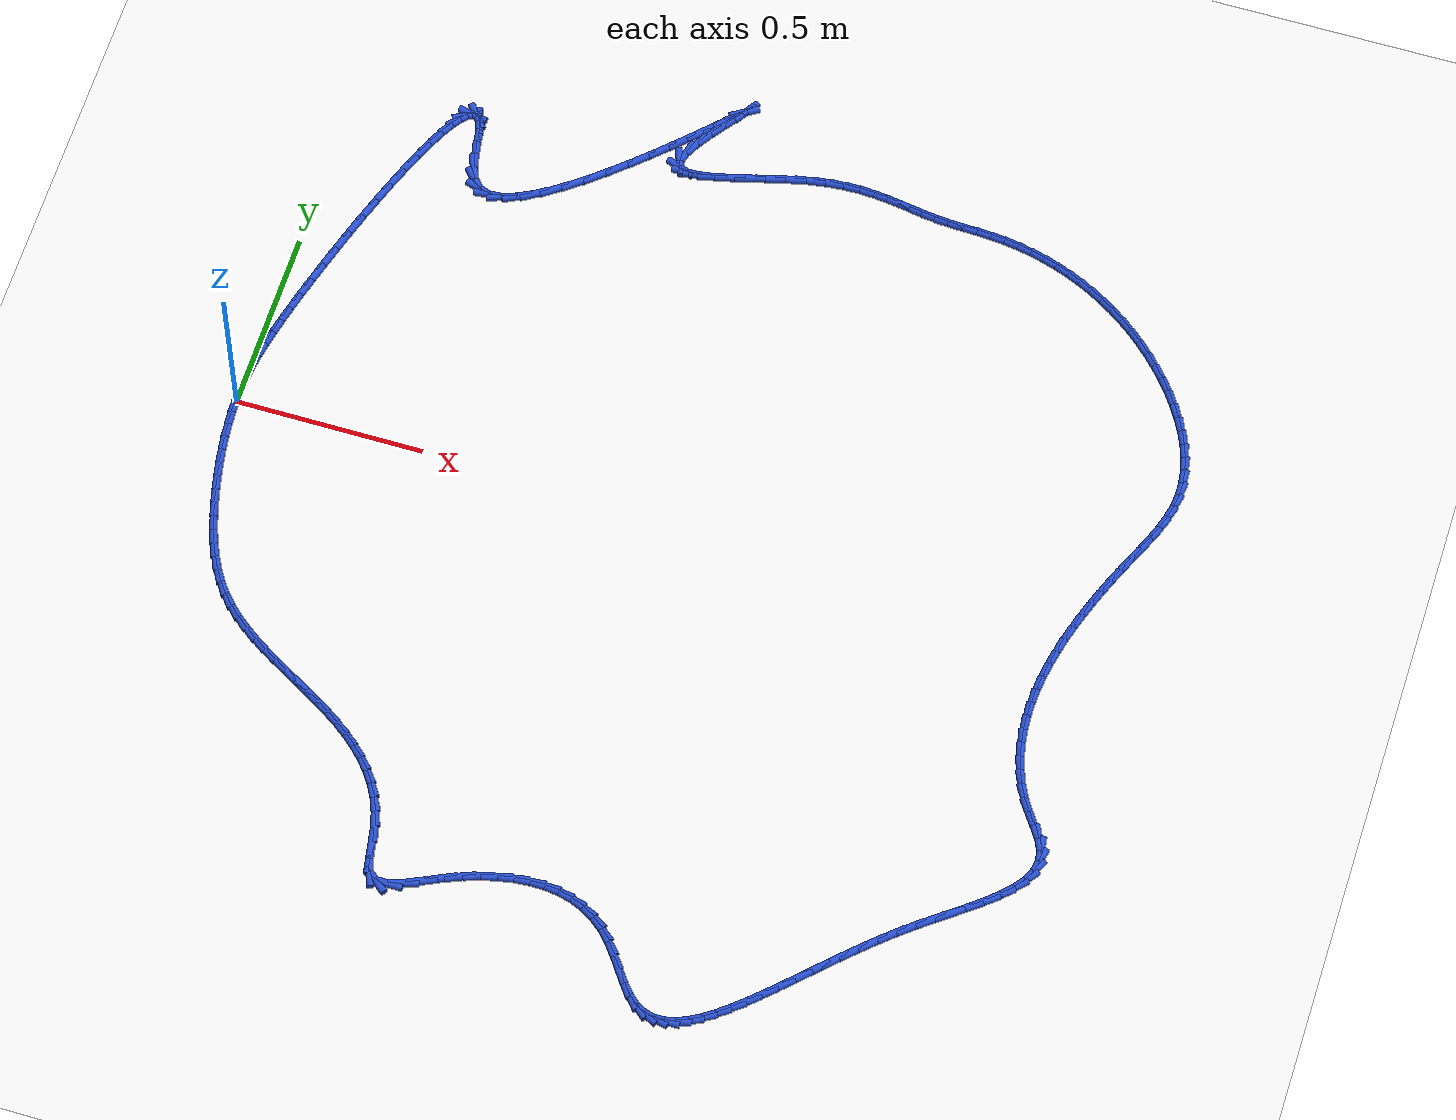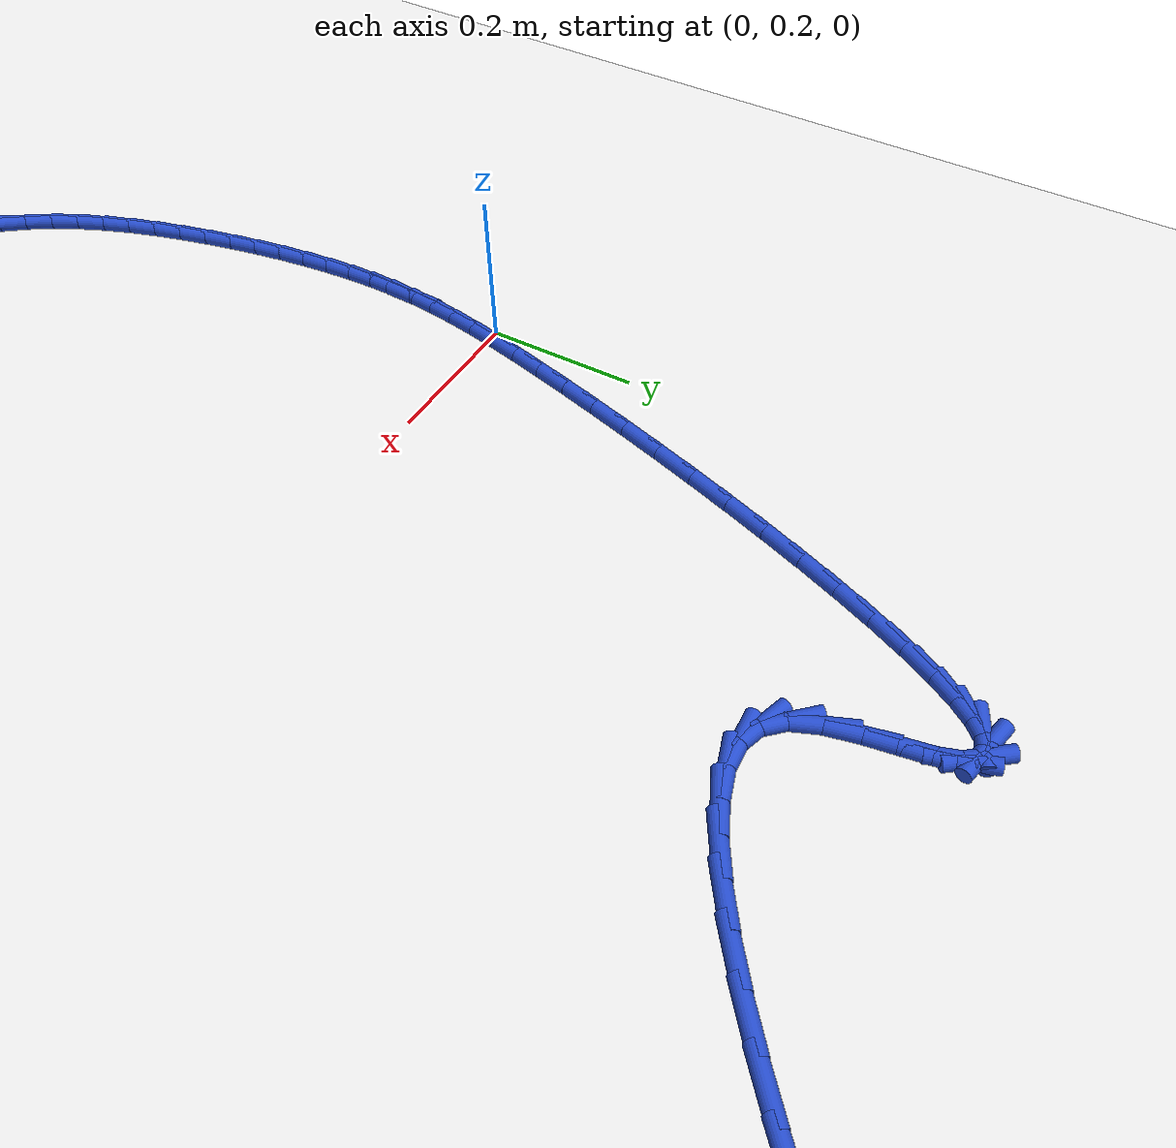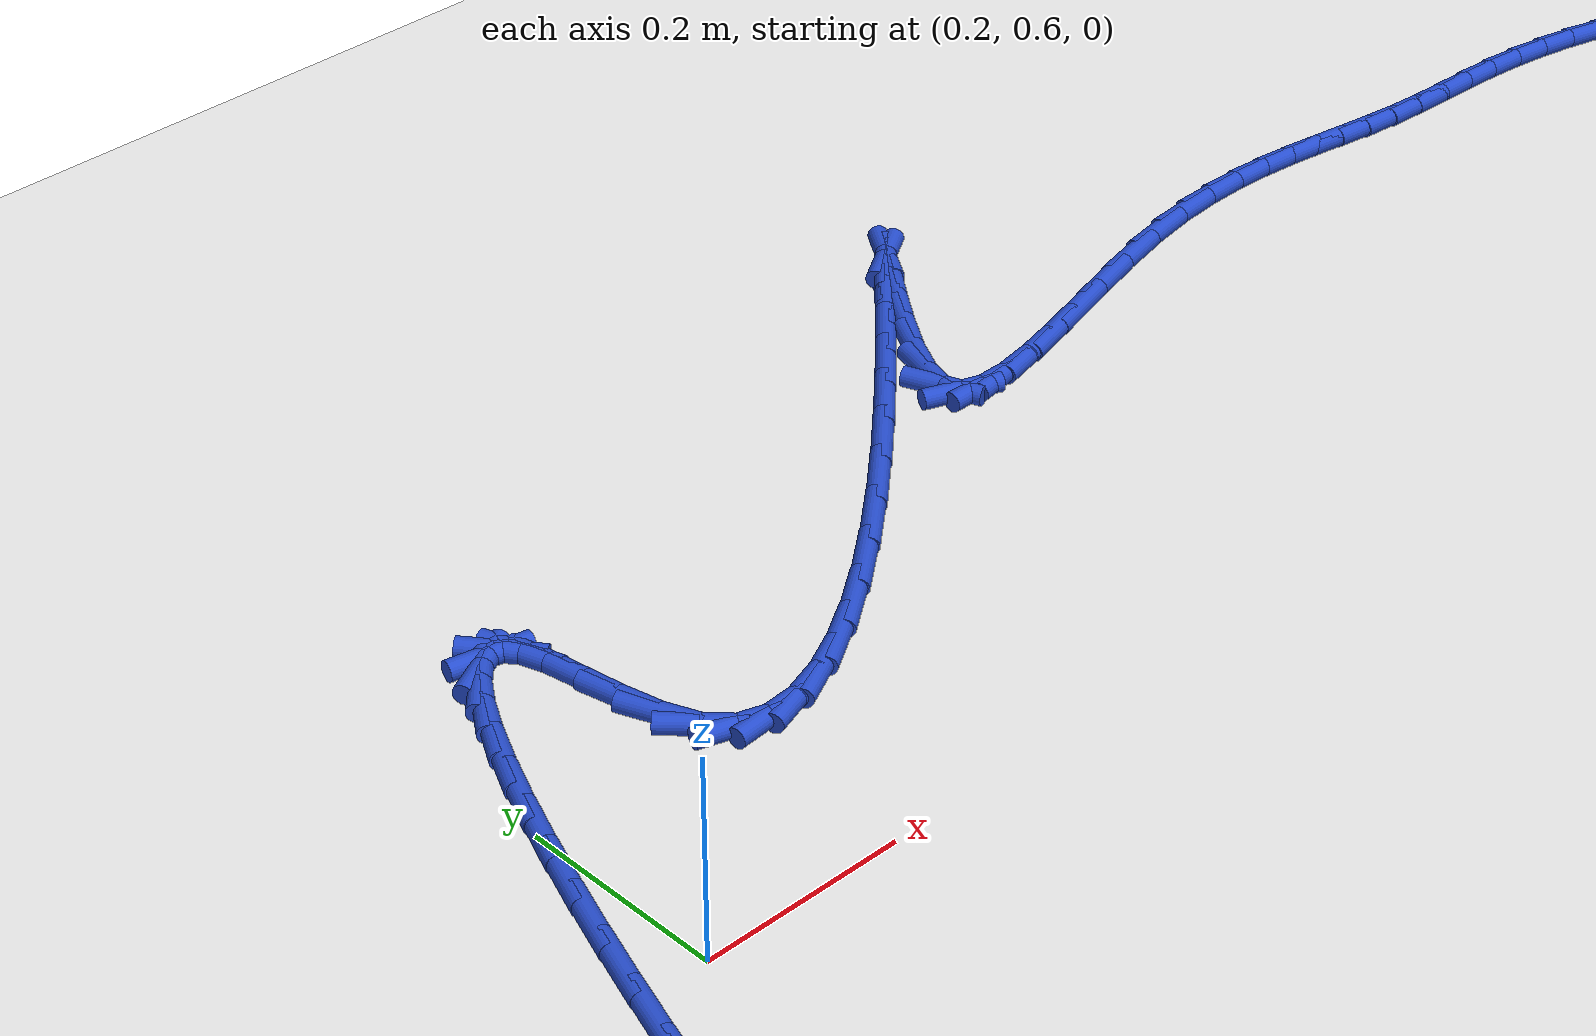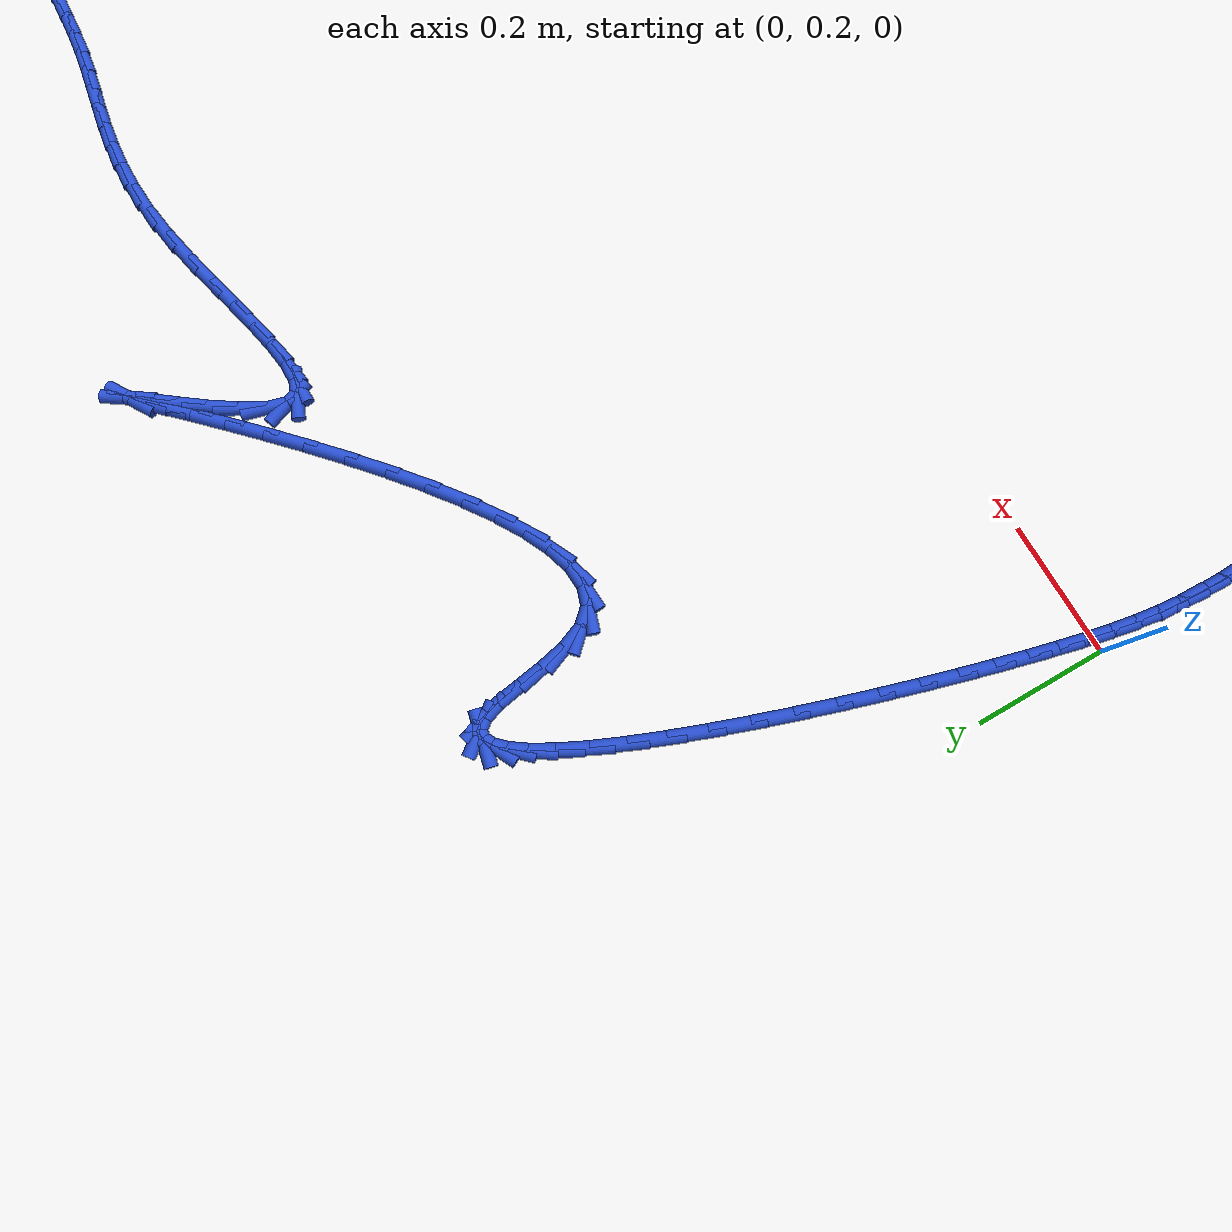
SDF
<sdf version="1.6">
 <world name="default">
  <light name="sun" type="directional">
   <pose>0 0 10 0 -0 0</pose>
   <diffuse>0.8 0.8 0.8 1</diffuse>
   <specular>0.2 0.2 0.2 1</specular>
   <attenuation>
    <range>1000</range>
    <constant>0.9</constant>
    <linear>0.01</linear>
    <quadratic>0.001</quadratic>
   </attenuation>
   <direction>-0.5 0.1 -0.9</direction>
  </light>
  <model name="ground_plane">
   <static>1</static>
   <link name="link">
    <collision name="collision">
     <geometry><plane><normal>0 0 1</normal><size>100 100</size></plane></geometry>
     <surface><friction><ode><mu>100</mu><mu2>50</mu2></ode></friction></surface>
    </collision>
    <visual name="visual">
     <cast_shadows>0</cast_shadows>
     <geometry><plane><normal>0 0 1</normal><size>100 100</size></plane></geometry>
     <material>
      <script><uri>file://media/materials/scripts/gazebo.material</uri><name>Gazebo/WhiteGlow</name></script>
     </material>
    </visual>
   </link>
  </model>
  <gravity>0 0 -9.8</gravity>
  <magnetic_field>6e-06 2.3e-05 -4.2e-05</magnetic_field>
  <atmosphere type="adiabatic"/>
  <physics name="default_physics" default="0" type="ode">
   <max_step_size>0.001</max_step_size>
   <real_time_factor>1</real_time_factor>
   <real_time_update_rate>1000</real_time_update_rate>
  </physics>
  <scene><ambient>0.4 0.4 0.4 1</ambient><background>0.7 0.7 0.7 1</background><shadows>1</shadows></scene>
  <spherical_coordinates>
   <surface_model>EARTH_WGS84</surface_model>
   <latitude_deg>0</latitude_deg>
   <longitude_deg>0</longitude_deg>
   <elevation>0</elevation>
   <heading_deg>0</heading_deg>
  </spherical_coordinates>
  <model name="line">
   <link name="link_0">
    <pose>-1.1275702593849246e-17 2.7755575615628914e-17 0.01 0 1.57 1.5615434562124908</pose>
    <collision name="collision">
     <geometry><cylinder><radius>0.01</radius><length>0.08</length></cylinder></geometry>
    </collision>
    <visual name="visual">
     <material>
      <script><name>Gazebo/Blue</name><uri>file://media/materials/scripts/gazebo.material</uri></script>
     </material>
     <geometry><cylinder><radius>0.01</radius><length>0.08</length></cylinder></geometry>
    </visual>
   </link>
   <link name="link_1">
    <pose>0.00032071212133747757 0.03465983510457822 0.01 0 1.57 1.5175648516688518</pose>
    <collision name="collision">
     <geometry><cylinder><radius>0.01</radius><length>0.08</length></cylinder></geometry>
    </collision>
    <visual name="visual">
     <material>
      <script><name>Gazebo/Blue</name><uri>file://media/materials/scripts/gazebo.material</uri></script>
     </material>
     <geometry><cylinder><radius>0.01</radius><length>0.08</length></cylinder></geometry>
    </visual>
   </link>
   <link name="link_2">
    <pose>0.0021454302282572194 0.06890638333522675 0.01 0 1.57 1.4738721594035114</pose>
    <collision name="collision">
     <geometry><cylinder><radius>0.01</radius><length>0.08</length></cylinder></geometry>
    </collision>
    <visual name="visual">
     <material>
      <script><name>Gazebo/Blue</name><uri>file://media/materials/scripts/gazebo.material</uri></script>
     </material>
     <geometry><cylinder><radius>0.01</radius><length>0.08</length></cylinder></geometry>
    </visual>
   </link>
   <link name="link_3">
    <pose>0.005502948103826773 0.10343850817212616 0.01 0 1.57 1.4331699964217521</pose>
    <collision name="collision">
     <geometry><cylinder><radius>0.01</radius><length>0.08</length></cylinder></geometry>
    </collision>
    <visual name="visual">
     <material>
      <script><name>Gazebo/Blue</name><uri>file://media/materials/scripts/gazebo.material</uri></script>
     </material>
     <geometry><cylinder><radius>0.01</radius><length>0.08</length></cylinder></geometry>
    </visual>
   </link>
   <link name="link_4">
    <pose>0.010422059531113696 0.13895507309545704 0.01 0 1.57 1.3975631338886407</pose>
    <collision name="collision">
     <geometry><cylinder><radius>0.01</radius><length>0.08</length></cylinder></geometry>
    </collision>
    <visual name="visual">
     <material>
      <script><name>Gazebo/Blue</name><uri>file://media/materials/scripts/gazebo.material</uri></script>
     </material>
     <geometry><cylinder><radius>0.01</radius><length>0.08</length></cylinder></geometry>
    </visual>
   </link>
   <link name="link_5">
    <pose>0.016931558293185545 0.1761549415853999 0.01 0 1.57 1.3682495324275081</pose>
    <collision name="collision">
     <geometry><cylinder><radius>0.01</radius><length>0.08</length></cylinder></geometry>
    </collision>
    <visual name="visual">
     <material>
      <script><name>Gazebo/Blue</name><uri>file://media/materials/scripts/gazebo.material</uri></script>
     </material>
     <geometry><cylinder><radius>0.01</radius><length>0.08</length></cylinder></geometry>
    </visual>
   </link>
   <link name="link_6">
    <pose>0.025060238173109865 0.21573697712213524 0.01 0 1.57 1.3455261808817527</pose>
    <collision name="collision">
     <geometry><cylinder><radius>0.01</radius><length>0.08</length></cylinder></geometry>
    </collision>
    <visual name="visual">
     <material>
      <script><name>Gazebo/Blue</name><uri>file://media/materials/scripts/gazebo.material</uri></script>
     </material>
     <geometry><cylinder><radius>0.01</radius><length>0.08</length></cylinder></geometry>
    </visual>
   </link>
   <link name="link_7">
    <pose>0.034836892953954215 0.2584000431858437 0.01 0 1.57 1.3289492586308602</pose>
    <collision name="collision">
     <geometry><cylinder><radius>0.01</radius><length>0.08</length></cylinder></geometry>
    </collision>
    <visual name="visual">
     <material>
      <script><name>Gazebo/Blue</name><uri>file://media/materials/scripts/gazebo.material</uri></script>
     </material>
     <geometry><cylinder><radius>0.01</radius><length>0.08</length></cylinder></geometry>
    </visual>
   </link>
   <link name="link_8">
    <pose>0.046286000577976216 0.3048137250771371 0.01 0 1.57 1.3162398495861478</pose>
    <collision name="collision">
     <geometry><cylinder><radius>0.01</radius><length>0.08</length></cylinder></geometry>
    </collision>
    <visual name="visual">
     <material>
      <script><name>Gazebo/Blue</name><uri>file://media/materials/scripts/gazebo.material</uri></script>
     </material>
     <geometry><cylinder><radius>0.01</radius><length>0.08</length></cylinder></geometry>
    </visual>
   </link>
   <link name="link_9">
    <pose>0.059326184572193526 0.3549295036266064 0.01 0 1.57 1.3049176117603984</pose>
    <collision name="collision">
     <geometry><cylinder><radius>0.01</radius><length>0.08</length></cylinder></geometry>
    </collision>
    <visual name="visual">
     <material>
      <script><name>Gazebo/Blue</name><uri>file://media/materials/scripts/gazebo.material</uri></script>
     </material>
     <geometry><cylinder><radius>0.01</radius><length>0.08</length></cylinder></geometry>
    </visual>
   </link>
   <link name="link_10">
    <pose>0.07376641805515838 0.4079550036029085 0.01 0 1.57 1.294193274917039</pose>
    <collision name="collision">
     <geometry><cylinder><radius>0.01</radius><length>0.08</length></cylinder></geometry>
    </collision>
    <visual name="visual">
     <material>
      <script><name>Gazebo/Blue</name><uri>file://media/materials/scripts/gazebo.material</uri></script>
     </material>
     <geometry><cylinder><radius>0.01</radius><length>0.08</length></cylinder></geometry>
    </visual>
   </link>
   <link name="link_11">
    <pose>0.0894105988105263 0.4630634192725063 0.01 0 1.57 1.2835333036569392</pose>
    <collision name="collision">
     <geometry><cylinder><radius>0.01</radius><length>0.08</length></cylinder></geometry>
    </collision>
    <visual name="visual">
     <material>
      <script><name>Gazebo/Blue</name><uri>file://media/materials/scripts/gazebo.material</uri></script>
     </material>
     <geometry><cylinder><radius>0.01</radius><length>0.08</length></cylinder></geometry>
    </visual>
   </link>
   <link name="link_12">
    <pose>0.10606262462195287 0.519427944901863 0.01 0 1.57 1.272478453742747</pose>
    <collision name="collision">
     <geometry><cylinder><radius>0.01</radius><length>0.08</length></cylinder></geometry>
    </collision>
    <visual name="visual">
     <material>
      <script><name>Gazebo/Blue</name><uri>file://media/materials/scripts/gazebo.material</uri></script>
     </material>
     <geometry><cylinder><radius>0.01</radius><length>0.08</length></cylinder></geometry>
    </visual>
   </link>
   <link name="link_13">
    <pose>0.12352639327309364 0.5762217747574414 0.01 0 1.57 1.260569366674199</pose>
    <collision name="collision">
     <geometry><cylinder><radius>0.01</radius><length>0.08</length></cylinder></geometry>
    </collision>
    <visual name="visual">
     <material>
      <script><name>Gazebo/Blue</name><uri>file://media/materials/scripts/gazebo.material</uri></script>
     </material>
     <geometry><cylinder><radius>0.01</radius><length>0.08</length></cylinder></geometry>
    </visual>
   </link>
   <link name="link_14">
    <pose>0.14160580254760402 0.6326181031057043 0.01 0 1.57 1.24728058162358</pose>
    <collision name="collision">
     <geometry><cylinder><radius>0.01</radius><length>0.08</length></cylinder></geometry>
    </collision>
    <visual name="visual">
     <material>
      <script><name>Gazebo/Blue</name><uri>file://media/materials/scripts/gazebo.material</uri></script>
     </material>
     <geometry><cylinder><radius>0.01</radius><length>0.08</length></cylinder></geometry>
    </visual>
   </link>
   <link name="link_15">
    <pose>0.16010475022913975 0.6877901242131153 0.01 0 1.57 1.2319418918140035</pose>
    <collision name="collision">
     <geometry><cylinder><radius>0.01</radius><length>0.08</length></cylinder></geometry>
    </collision>
    <visual name="visual">
     <material>
      <script><name>Gazebo/Blue</name><uri>file://media/materials/scripts/gazebo.material</uri></script>
     </material>
     <geometry><cylinder><radius>0.01</radius><length>0.08</length></cylinder></geometry>
    </visual>
   </link>
   <link name="link_16">
    <pose>0.17882713410135623 0.7409110323461364 0.01 0 1.57 1.2136215446589431</pose>
    <collision name="collision">
     <geometry><cylinder><radius>0.01</radius><length>0.08</length></cylinder></geometry>
    </collision>
    <visual name="visual">
     <material>
      <script><name>Gazebo/Blue</name><uri>file://media/materials/scripts/gazebo.material</uri></script>
     </material>
     <geometry><cylinder><radius>0.01</radius><length>0.08</length></cylinder></geometry>
    </visual>
   </link>
   <link name="link_17">
    <pose>0.197576851947909 0.7911540217712314 0.01 0 1.57 1.1909265250723264</pose>
    <collision name="collision">
     <geometry><cylinder><radius>0.01</radius><length>0.08</length></cylinder></geometry>
    </collision>
    <visual name="visual">
     <material>
      <script><name>Gazebo/Blue</name><uri>file://media/materials/scripts/gazebo.material</uri></script>
     </material>
     <geometry><cylinder><radius>0.01</radius><length>0.08</length></cylinder></geometry>
    </visual>
   </link>
   <link name="link_18">
    <pose>0.2161578015524537 0.8376922867548631 0.01 0 1.57 1.16162475773444</pose>
    <collision name="collision">
     <geometry><cylinder><radius>0.01</radius><length>0.08</length></cylinder></geometry>
    </collision>
    <visual name="visual">
     <material>
      <script><name>Gazebo/Blue</name><uri>file://media/materials/scripts/gazebo.material</uri></script>
     </material>
     <geometry><cylinder><radius>0.01</radius><length>0.08</length></cylinder></geometry>
    </visual>
   </link>
   <link name="link_19">
    <pose>0.2343738806986458 0.8796990215634941 0.01 0 1.57 1.1218607726843712</pose>
    <collision name="collision">
     <geometry><cylinder><radius>0.01</radius><length>0.08</length></cylinder></geometry>
    </collision>
    <visual name="visual">
     <material>
      <script><name>Gazebo/Blue</name><uri>file://media/materials/scripts/gazebo.material</uri></script>
     </material>
     <geometry><cylinder><radius>0.01</radius><length>0.08</length></cylinder></geometry>
    </visual>
   </link>
   <link name="link_20">
    <pose>0.2520289871701408 0.9163474204635876 0.01 0 1.57 1.0643502575124055</pose>
    <collision name="collision">
     <geometry><cylinder><radius>0.01</radius><length>0.08</length></cylinder></geometry>
    </collision>
    <visual name="visual">
     <material>
      <script><name>Gazebo/Blue</name><uri>file://media/materials/scripts/gazebo.material</uri></script>
     </material>
     <geometry><cylinder><radius>0.01</radius><length>0.08</length></cylinder></geometry>
    </visual>
   </link>
   <link name="link_21">
    <pose>0.2689270187505943 0.9468106777216067 0.01 0 1.57 0.9736790452168863</pose>
    <collision name="collision">
     <geometry><cylinder><radius>0.01</radius><length>0.08</length></cylinder></geometry>
    </collision>
    <visual name="visual">
     <material>
      <script><name>Gazebo/Blue</name><uri>file://media/materials/scripts/gazebo.material</uri></script>
     </material>
     <geometry><cylinder><radius>0.01</radius><length>0.08</length></cylinder></geometry>
    </visual>
   </link>
   <link name="link_22">
    <pose>0.28487187322366186 0.9702619876040144 0.01 0 1.57 0.8122589101393465</pose>
    <collision name="collision">
     <geometry><cylinder><radius>0.01</radius><length>0.08</length></cylinder></geometry>
    </collision>
    <visual name="visual">
     <material>
      <script><name>Gazebo/Blue</name><uri>file://media/materials/scripts/gazebo.material</uri></script>
     </material>
     <geometry><cylinder><radius>0.01</radius><length>0.08</length></cylinder></geometry>
    </visual>
   </link>
   <link name="link_23">
    <pose>0.29966744837299897 0.9858745443772732 0.01 0 1.57 0.47675871993557756</pose>
    <collision name="collision">
     <geometry><cylinder><radius>0.01</radius><length>0.08</length></cylinder></geometry>
    </collision>
    <visual name="visual">
     <material>
      <script><name>Gazebo/Blue</name><uri>file://media/materials/scripts/gazebo.material</uri></script>
     </material>
     <geometry><cylinder><radius>0.01</radius><length>0.08</length></cylinder></geometry>
    </visual>
   </link>
   <link name="link_24">
    <pose>0.31311764198226116 0.9928215423078464 0.01 0 1.57 -0.21057143866437256</pose>
    <collision name="collision">
     <geometry><cylinder><radius>0.01</radius><length>0.08</length></cylinder></geometry>
    </collision>
    <visual name="visual">
     <material>
      <script><name>Gazebo/Blue</name><uri>file://media/materials/scripts/gazebo.material</uri></script>
     </material>
     <geometry><cylinder><radius>0.01</radius><length>0.08</length></cylinder></geometry>
    </visual>
   </link>
   <link name="link_25">
    <pose>0.32502635183510403 0.9902761756621971 0.01 0 1.57 -0.9017932951318166</pose>
    <collision name="collision">
     <geometry><cylinder><radius>0.01</radius><length>0.08</length></cylinder></geometry>
    </collision>
    <visual name="visual">
     <material>
      <script><name>Gazebo/Blue</name><uri>file://media/materials/scripts/gazebo.material</uri></script>
     </material>
     <geometry><cylinder><radius>0.01</radius><length>0.08</length></cylinder></geometry>
    </visual>
   </link>
   <link name="link_26">
    <pose>0.33519747571518316 0.9774116387067882 0.01 0 1.57 -1.2403026367977674</pose>
    <collision name="collision">
     <geometry><cylinder><radius>0.01</radius><length>0.08</length></cylinder></geometry>
    </collision>
    <visual name="visual">
     <material>
      <script><name>Gazebo/Blue</name><uri>file://media/materials/scripts/gazebo.material</uri></script>
     </material>
     <geometry><cylinder><radius>0.01</radius><length>0.08</length></cylinder></geometry>
    </visual>
   </link>
   <link name="link_27">
    <pose>0.3434349158871429 0.9534011383127101 0.01 0 1.57 -1.3845847862296412</pose>
    <collision name="collision">
     <geometry><cylinder><radius>0.01</radius><length>0.08</length></cylinder></geometry>
    </collision>
    <visual name="visual">
     <material>
      <script><name>Gazebo/Blue</name><uri>file://media/materials/scripts/gazebo.material</uri></script>
     </material>
     <geometry><cylinder><radius>0.01</radius><length>0.08</length></cylinder></geometry>
    </visual>
   </link>
   <link name="link_28">
    <pose>0.34998139979266796 0.9186522579681649 0.01 0 1.57 -1.405711516225509</pose>
    <collision name="collision">
     <geometry><cylinder><radius>0.01</radius><length>0.08</length></cylinder></geometry>
    </collision>
    <visual name="visual">
     <material>
      <script><name>Gazebo/Blue</name><uri>file://media/materials/scripts/gazebo.material</uri></script>
     </material>
     <geometry><cylinder><radius>0.01</radius><length>0.08</length></cylinder></geometry>
    </visual>
   </link>
   <link name="link_29">
    <pose>0.35672204181034156 0.8781924711248926 0.01 0 1.57 -1.3449726657483514</pose>
    <collision name="collision">
     <geometry><cylinder><radius>0.01</radius><length>0.08</length></cylinder></geometry>
    </collision>
    <visual name="visual">
     <material>
      <script><name>Gazebo/Blue</name><uri>file://media/materials/scripts/gazebo.material</uri></script>
     </material>
     <geometry><cylinder><radius>0.01</radius><length>0.08</length></cylinder></geometry>
    </visual>
   </link>
   <link name="link_30">
    <pose>0.36592611855934754 0.8381298658205449 0.01 0 1.57 -1.1771594271546988</pose>
    <collision name="collision">
     <geometry><cylinder><radius>0.01</radius><length>0.08</length></cylinder></geometry>
    </collision>
    <visual name="visual">
     <material>
      <script><name>Gazebo/Blue</name><uri>file://media/materials/scripts/gazebo.material</uri></script>
     </material>
     <geometry><cylinder><radius>0.01</radius><length>0.08</length></cylinder></geometry>
    </visual>
   </link>
   <link name="link_31">
    <pose>0.3798629066588702 0.8045725300927744 0.01 0 1.57 -0.8067428693570016</pose>
    <collision name="collision">
     <geometry><cylinder><radius>0.01</radius><length>0.08</length></cylinder></geometry>
    </collision>
    <visual name="visual">
     <material>
      <script><name>Gazebo/Blue</name><uri>file://media/materials/scripts/gazebo.material</uri></script>
     </material>
     <geometry><cylinder><radius>0.01</radius><length>0.08</length></cylinder></geometry>
    </visual>
   </link>
   <link name="link_32">
    <pose>0.4005323697471649 0.7830013152043961 0.01 0 1.57 -0.3121802786575847</pose>
    <collision name="collision">
     <geometry><cylinder><radius>0.01</radius><length>0.08</length></cylinder></geometry>
    </collision>
    <visual name="visual">
     <material>
      <script><name>Gazebo/Blue</name><uri>file://media/materials/scripts/gazebo.material</uri></script>
     </material>
     <geometry><cylinder><radius>0.01</radius><length>0.08</length></cylinder></geometry>
    </visual>
   </link>
   <link name="link_33">
    <pose>0.42790382237705316 0.774167639106917 0.01 0 1.57 0.0752962812371527</pose>
    <collision name="collision">
     <geometry><cylinder><radius>0.01</radius><length>0.08</length></cylinder></geometry>
    </collision>
    <visual name="visual">
     <material>
      <script><name>Gazebo/Blue</name><uri>file://media/materials/scripts/gazebo.material</uri></script>
     </material>
     <geometry><cylinder><radius>0.01</radius><length>0.08</length></cylinder></geometry>
    </visual>
   </link>
   <link name="link_34">
    <pose>0.461020440954838 0.7766659204788328 0.01 0 1.57 0.3165231054946374</pose>
    <collision name="collision">
     <geometry><cylinder><radius>0.01</radius><length>0.08</length></cylinder></geometry>
    </collision>
    <visual name="visual">
     <material>
      <script><name>Gazebo/Blue</name><uri>file://media/materials/scripts/gazebo.material</uri></script>
     </material>
     <geometry><cylinder><radius>0.01</radius><length>0.08</length></cylinder></geometry>
    </visual>
   </link>
   <link name="link_35">
    <pose>0.49892067936838297 0.7890795791332124 0.01 0 1.57 0.4646307653863084</pose>
    <collision name="collision">
     <geometry><cylinder><radius>0.01</radius><length>0.08</length></cylinder></geometry>
    </collision>
    <visual name="visual">
     <material>
      <script><name>Gazebo/Blue</name><uri>file://media/materials/scripts/gazebo.material</uri></script>
     </material>
     <geometry><cylinder><radius>0.01</radius><length>0.08</length></cylinder></geometry>
    </visual>
   </link>
   <link name="link_36">
    <pose>0.5406429915055511 0.8099920348831242 0.01 0 1.57 0.5606998091053702</pose>
    <collision name="collision">
     <geometry><cylinder><radius>0.01</radius><length>0.08</length></cylinder></geometry>
    </collision>
    <visual name="visual">
     <material>
      <script><name>Gazebo/Blue</name><uri>file://media/materials/scripts/gazebo.material</uri></script>
     </material>
     <geometry><cylinder><radius>0.01</radius><length>0.08</length></cylinder></geometry>
    </visual>
   </link>
   <link name="link_37">
    <pose>0.5852258312542055 0.8379867075416358 0.01 0 1.57 0.6267578541160936</pose>
    <collision name="collision">
     <geometry><cylinder><radius>0.01</radius><length>0.08</length></cylinder></geometry>
    </collision>
    <visual name="visual">
     <material>
      <script><name>Gazebo/Blue</name><uri>file://media/materials/scripts/gazebo.material</uri></script>
     </material>
     <geometry><cylinder><radius>0.01</radius><length>0.08</length></cylinder></geometry>
    </visual>
   </link>
   <link name="link_38">
    <pose>0.6317076525022097 0.8716470169218161 0.01 0 1.57 0.674406016422861</pose>
    <collision name="collision">
     <geometry><cylinder><radius>0.01</radius><length>0.08</length></cylinder></geometry>
    </collision>
    <visual name="visual">
     <material>
      <script><name>Gazebo/Blue</name><uri>file://media/materials/scripts/gazebo.material</uri></script>
     </material>
     <geometry><cylinder><radius>0.01</radius><length>0.08</length></cylinder></geometry>
    </visual>
   </link>
   <link name="link_39">
    <pose>0.6791269091374263 0.9095563828367328 0.01 0 1.57 0.7100528522402593</pose>
    <collision name="collision">
     <geometry><cylinder><radius>0.01</radius><length>0.08</length></cylinder></geometry>
    </collision>
    <visual name="visual">
     <material>
      <script><name>Gazebo/Blue</name><uri>file://media/materials/scripts/gazebo.material</uri></script>
     </material>
     <geometry><cylinder><radius>0.01</radius><length>0.08</length></cylinder></geometry>
    </visual>
   </link>
   <link name="link_40">
    <pose>0.7265220550477194 0.9502982250994547 0.01 0 1.57 0.7374290767563527</pose>
    <collision name="collision">
     <geometry><cylinder><radius>0.01</radius><length>0.08</length></cylinder></geometry>
    </collision>
    <visual name="visual">
     <material>
      <script><name>Gazebo/Blue</name><uri>file://media/materials/scripts/gazebo.material</uri></script>
     </material>
     <geometry><cylinder><radius>0.01</radius><length>0.08</length></cylinder></geometry>
    </visual>
   </link>
   <link name="link_41">
    <pose>0.7729315441209513 0.9924559635230493 0.01 0 1.57 0.7587910834901544</pose>
    <collision name="collision">
     <geometry><cylinder><radius>0.01</radius><length>0.08</length></cylinder></geometry>
    </collision>
    <visual name="visual">
     <material>
      <script><name>Gazebo/Blue</name><uri>file://media/materials/scripts/gazebo.material</uri></script>
     </material>
     <geometry><cylinder><radius>0.01</radius><length>0.08</length></cylinder></geometry>
    </visual>
   </link>
   <link name="link_42">
    <pose>0.817393830244986 1.034613017920586 0.01 0 1.57 0.7755101155539222</pose>
    <collision name="collision">
     <geometry><cylinder><radius>0.01</radius><length>0.08</length></cylinder></geometry>
    </collision>
    <visual name="visual">
     <material>
      <script><name>Gazebo/Blue</name><uri>file://media/materials/scripts/gazebo.material</uri></script>
     </material>
     <geometry><cylinder><radius>0.01</radius><length>0.08</length></cylinder></geometry>
    </visual>
   </link>
   <link name="link_43">
    <pose>0.8589473673076864 1.0753528081051322 0.01 0 1.57 0.7883443949666793</pose>
    <collision name="collision">
     <geometry><cylinder><radius>0.01</radius><length>0.08</length></cylinder></geometry>
    </collision>
    <visual name="visual">
     <material>
      <script><name>Gazebo/Blue</name><uri>file://media/materials/scripts/gazebo.material</uri></script>
     </material>
     <geometry><cylinder><radius>0.01</radius><length>0.08</length></cylinder></geometry>
    </visual>
   </link>
   <link name="link_44">
    <pose>0.8966306091969158 1.1132587538897567 0.01 0 1.57 0.7974883547913829</pose>
    <collision name="collision">
     <geometry><cylinder><radius>0.01</radius><length>0.08</length></cylinder></geometry>
    </collision>
    <visual name="visual">
     <material>
      <script><name>Gazebo/Blue</name><uri>file://media/materials/scripts/gazebo.material</uri></script>
     </material>
     <geometry><cylinder><radius>0.01</radius><length>0.08</length></cylinder></geometry>
    </visual>
   </link>
   <link name="link_45">
    <pose>0.9294820098005373 1.1469142750875272 0.01 0 1.57 0.8023004933216228</pose>
    <collision name="collision">
     <geometry><cylinder><radius>0.01</radius><length>0.08</length></cylinder></geometry>
    </collision>
    <visual name="visual">
     <material>
      <script><name>Gazebo/Blue</name><uri>file://media/materials/scripts/gazebo.material</uri></script>
     </material>
     <geometry><cylinder><radius>0.01</radius><length>0.08</length></cylinder></geometry>
    </visual>
   </link>
   <link name="link_46">
    <pose>0.9565400230064144 1.1749027915115127 0.01 0 1.57 0.8000023377243067</pose>
    <collision name="collision">
     <geometry><cylinder><radius>0.01</radius><length>0.08</length></cylinder></geometry>
    </collision>
    <visual name="visual">
     <material>
      <script><name>Gazebo/Blue</name><uri>file://media/materials/scripts/gazebo.material</uri></script>
     </material>
     <geometry><cylinder><radius>0.01</radius><length>0.08</length></cylinder></geometry>
    </visual>
   </link>
   <link name="link_47">
    <pose>0.9768431027024098 1.1958077229747806 0.01 0 1.57 0.7781224287706942</pose>
    <collision name="collision">
     <geometry><cylinder><radius>0.01</radius><length>0.08</length></cylinder></geometry>
    </collision>
    <visual name="visual">
     <material>
      <script><name>Gazebo/Blue</name><uri>file://media/materials/scripts/gazebo.material</uri></script>
     </material>
     <geometry><cylinder><radius>0.01</radius><length>0.08</length></cylinder></geometry>
    </visual>
   </link>
   <link name="link_48">
    <pose>0.9894297027763872 1.2082124892903996 0.01 0 1.57 0.5668651279600222</pose>
    <collision name="collision">
     <geometry><cylinder><radius>0.01</radius><length>0.08</length></cylinder></geometry>
    </collision>
    <visual name="visual">
     <material>
      <script><name>Gazebo/Blue</name><uri>file://media/materials/scripts/gazebo.material</uri></script>
     </material>
     <geometry><cylinder><radius>0.01</radius><length>0.08</length></cylinder></geometry>
    </visual>
   </link>
   <link name="link_49">
    <pose>0.9933382771162095 1.2107005102714379 0.01 0 1.57 0.9958888680821032</pose>
    <collision name="collision">
     <geometry><cylinder><radius>0.01</radius><length>0.08</length></cylinder></geometry>
    </collision>
    <visual name="visual">
     <material>
      <script><name>Gazebo/Blue</name><uri>file://media/materials/scripts/gazebo.material</uri></script>
     </material>
     <geometry><cylinder><radius>0.01</radius><length>0.08</length></cylinder></geometry>
    </visual>
   </link>
   <link name="link_50">
    <pose>0.9876072796097402 1.2018552057309635 0.01 0 1.57 0.9258488552155959</pose>
    <collision name="collision">
     <geometry><cylinder><radius>0.01</radius><length>0.08</length></cylinder></geometry>
    </collision>
    <visual name="visual">
     <material>
      <script><name>Gazebo/Blue</name><uri>file://media/materials/scripts/gazebo.material</uri></script>
     </material>
     <geometry><cylinder><radius>0.01</radius><length>0.08</length></cylinder></geometry>
    </visual>
   </link>
   <link name="link_51">
    <pose>0.9716697754355356 1.1806691086660293 0.01 0 1.57 0.9261754921088093</pose>
    <collision name="collision">
     <geometry><cylinder><radius>0.01</radius><length>0.08</length></cylinder></geometry>
    </collision>
    <visual name="visual">
     <material>
      <script><name>Gazebo/Blue</name><uri>file://media/materials/scripts/gazebo.material</uri></script>
     </material>
     <geometry><cylinder><radius>0.01</radius><length>0.08</length></cylinder></geometry>
    </visual>
   </link>
   <link name="link_52">
    <pose>0.9483569779739252 1.1496577816049334 0.01 0 1.57 0.9499174062546217</pose>
    <collision name="collision">
     <geometry><cylinder><radius>0.01</radius><length>0.08</length></cylinder></geometry>
    </collision>
    <visual name="visual">
     <material>
      <script><name>Gazebo/Blue</name><uri>file://media/materials/scripts/gazebo.material</uri></script>
     </material>
     <geometry><cylinder><radius>0.01</radius><length>0.08</length></cylinder></geometry>
    </visual>
   </link>
   <link name="link_53">
    <pose>0.922234461981296 1.113134885917725 0.01 0 1.57 0.9973423143154183</pose>
    <collision name="collision">
     <geometry><cylinder><radius>0.01</radius><length>0.08</length></cylinder></geometry>
    </collision>
    <visual name="visual">
     <material>
      <script><name>Gazebo/Blue</name><uri>file://media/materials/scripts/gazebo.material</uri></script>
     </material>
     <geometry><cylinder><radius>0.01</radius><length>0.08</length></cylinder></geometry>
    </visual>
   </link>
   <link name="link_54">
    <pose>0.8978816847349135 1.0754284756754546 0.01 0 1.57 1.090561967167285</pose>
    <collision name="collision">
     <geometry><cylinder><radius>0.01</radius><length>0.08</length></cylinder></geometry>
    </collision>
    <visual name="visual">
     <material>
      <script><name>Gazebo/Blue</name><uri>file://media/materials/scripts/gazebo.material</uri></script>
     </material>
     <geometry><cylinder><radius>0.01</radius><length>0.08</length></cylinder></geometry>
    </visual>
   </link>
   <link name="link_55">
    <pose>0.8798781035120424 1.040866604949171 0.01 0 1.57 1.315236159343471</pose>
    <collision name="collision">
     <geometry><cylinder><radius>0.01</radius><length>0.08</length></cylinder></geometry>
    </collision>
    <visual name="visual">
     <material>
      <script><name>Gazebo/Blue</name><uri>file://media/materials/scripts/gazebo.material</uri></script>
     </material>
     <geometry><cylinder><radius>0.01</radius><length>0.08</length></cylinder></geometry>
    </visual>
   </link>
   <link name="link_56">
    <pose>0.8727995449216921 1.013774038421928 0.01 0 1.57 -1.1876448813150118</pose>
    <collision name="collision">
     <geometry><cylinder><radius>0.01</radius><length>0.08</length></cylinder></geometry>
    </collision>
    <visual name="visual">
     <material>
      <script><name>Gazebo/Blue</name><uri>file://media/materials/scripts/gazebo.material</uri></script>
     </material>
     <geometry><cylinder><radius>0.01</radius><length>0.08</length></cylinder></geometry>
    </visual>
   </link>
   <link name="link_57">
    <pose>0.8795693819859149 0.9969784166635842 0.01 0 1.57 -0.3724080615252257</pose>
    <collision name="collision">
     <geometry><cylinder><radius>0.01</radius><length>0.08</length></cylinder></geometry>
    </collision>
    <visual name="visual">
     <material>
      <script><name>Gazebo/Blue</name><uri>file://media/materials/scripts/gazebo.material</uri></script>
     </material>
     <geometry><cylinder><radius>0.01</radius><length>0.08</length></cylinder></geometry>
    </visual>
   </link>
   <link name="link_58">
    <pose>0.898849837441317 0.9894467750853193 0.01 0 1.57 0.00287160540675507</pose>
    <collision name="collision">
     <geometry><cylinder><radius>0.01</radius><length>0.08</length></cylinder></geometry>
    </collision>
    <visual name="visual">
     <material>
      <script><name>Gazebo/Blue</name><uri>file://media/materials/scripts/gazebo.material</uri></script>
     </material>
     <geometry><cylinder><radius>0.01</radius><length>0.08</length></cylinder></geometry>
    </visual>
   </link>
   <link name="link_59">
    <pose>0.9286255742738972 0.9895322794872244 0.01 0 1.57 0.15699577477687965</pose>
    <collision name="collision">
     <geometry><cylinder><radius>0.01</radius><length>0.08</length></cylinder></geometry>
    </collision>
    <visual name="visual">
     <material>
      <script><name>Gazebo/Blue</name><uri>file://media/materials/scripts/gazebo.material</uri></script>
     </material>
     <geometry><cylinder><radius>0.01</radius><length>0.08</length></cylinder></geometry>
    </visual>
   </link>
   <link name="link_60">
    <pose>0.9668812554696541 0.9955880956693921 0.01 0 1.57 0.22805591061786093</pose>
    <collision name="collision">
     <geometry><cylinder><radius>0.01</radius><length>0.08</length></cylinder></geometry>
    </collision>
    <visual name="visual">
     <material>
      <script><name>Gazebo/Blue</name><uri>file://media/materials/scripts/gazebo.material</uri></script>
     </material>
     <geometry><cylinder><radius>0.01</radius><length>0.08</length></cylinder></geometry>
    </visual>
   </link>
   <link name="link_61">
    <pose>1.0116015440145871 1.0059673894319143 0.01 0 1.57 0.25953982782651713</pose>
    <collision name="collision">
     <geometry><cylinder><radius>0.01</radius><length>0.08</length></cylinder></geometry>
    </collision>
    <visual name="visual">
     <material>
      <script><name>Gazebo/Blue</name><uri>file://media/materials/scripts/gazebo.material</uri></script>
     </material>
     <geometry><cylinder><radius>0.01</radius><length>0.08</length></cylinder></geometry>
    </visual>
   </link>
   <link name="link_62">
    <pose>1.0607711028946938 1.019023326574883 0.01 0 1.57 0.266469681383502</pose>
    <collision name="collision">
     <geometry><cylinder><radius>0.01</radius><length>0.08</length></cylinder></geometry>
    </collision>
    <visual name="visual">
     <material>
      <script><name>Gazebo/Blue</name><uri>file://media/materials/scripts/gazebo.material</uri></script>
     </material>
     <geometry><cylinder><radius>0.01</radius><length>0.08</length></cylinder></geometry>
    </visual>
   </link>
   <link name="link_63">
    <pose>1.1123745950959743 1.03310907289839 0.01 0 1.57 0.2533410840350094</pose>
    <collision name="collision">
     <geometry><cylinder><radius>0.01</radius><length>0.08</length></cylinder></geometry>
    </collision>
    <visual name="visual">
     <material>
      <script><name>Gazebo/Blue</name><uri>file://media/materials/scripts/gazebo.material</uri></script>
     </material>
     <geometry><cylinder><radius>0.01</radius><length>0.08</length></cylinder></geometry>
    </visual>
   </link>
   <link name="link_64">
    <pose>1.164396683604426 1.0465777942025274 0.01 0 1.57 0.21865437996021253</pose>
    <collision name="collision">
     <geometry><cylinder><radius>0.01</radius><length>0.08</length></cylinder></geometry>
    </collision>
    <visual name="visual">
     <material>
      <script><name>Gazebo/Blue</name><uri>file://media/materials/scripts/gazebo.material</uri></script>
     </material>
     <geometry><cylinder><radius>0.01</radius><length>0.08</length></cylinder></geometry>
    </visual>
   </link>
   <link name="link_65">
    <pose>1.2148220314060487 1.0577826562873878 0.01 0 1.57 0.1578361658310611</pose>
    <collision name="collision">
     <geometry><cylinder><radius>0.01</radius><length>0.08</length></cylinder></geometry>
    </collision>
    <visual name="visual">
     <material>
      <script><name>Gazebo/Blue</name><uri>file://media/materials/scripts/gazebo.material</uri></script>
     </material>
     <geometry><cylinder><radius>0.01</radius><length>0.08</length></cylinder></geometry>
    </visual>
   </link>
   <link name="link_66">
    <pose>1.26185294058029 1.065268097892469 0.01 0 1.57 0.08597641374929144</pose>
    <collision name="collision">
     <geometry><cylinder><radius>0.01</radius><length>0.08</length></cylinder></geometry>
    </collision>
    <visual name="visual">
     <material>
      <script><name>Gazebo/Blue</name><uri>file://media/materials/scripts/gazebo.material</uri></script>
     </material>
     <geometry><cylinder><radius>0.01</radius><length>0.08</length></cylinder></geometry>
    </visual>
   </link>
   <link name="link_67">
    <pose>1.3053261710530084 1.069015007209732 0.01 0 1.57 0.01585553881359983</pose>
    <collision name="collision">
     <geometry><cylinder><radius>0.01</radius><length>0.08</length></cylinder></geometry>
    </collision>
    <visual name="visual">
     <material>
      <script><name>Gazebo/Blue</name><uri>file://media/materials/scripts/gazebo.material</uri></script>
     </material>
     <geometry><cylinder><radius>0.01</radius><length>0.08</length></cylinder></geometry>
    </visual>
   </link>
   <link name="link_68">
    <pose>1.3458213381599664 1.0696571337142582 0.01 0 1.57 -0.04787957326140812</pose>
    <collision name="collision">
     <geometry><cylinder><radius>0.01</radius><length>0.08</length></cylinder></geometry>
    </collision>
    <visual name="visual">
     <material>
      <script><name>Gazebo/Blue</name><uri>file://media/materials/scripts/gazebo.material</uri></script>
     </material>
     <geometry><cylinder><radius>0.01</radius><length>0.08</length></cylinder></geometry>
    </visual>
   </link>
   <link name="link_69">
    <pose>1.3839217874486645 1.067831505191807 0.01 0 1.57 -0.10041747998975852</pose>
    <collision name="collision">
     <geometry><cylinder><radius>0.01</radius><length>0.08</length></cylinder></geometry>
    </collision>
    <visual name="visual">
     <material>
      <script><name>Gazebo/Blue</name><uri>file://media/materials/scripts/gazebo.material</uri></script>
     </material>
     <geometry><cylinder><radius>0.01</radius><length>0.08</length></cylinder></geometry>
    </visual>
   </link>
   <link name="link_70">
    <pose>1.4202108644666065 1.0641751494281386 0.01 0 1.57 -0.13745935292737266</pose>
    <collision name="collision">
     <geometry><cylinder><radius>0.01</radius><length>0.08</length></cylinder></geometry>
    </collision>
    <visual name="visual">
     <material>
      <script><name>Gazebo/Blue</name><uri>file://media/materials/scripts/gazebo.material</uri></script>
     </material>
     <geometry><cylinder><radius>0.01</radius><length>0.08</length></cylinder></geometry>
    </visual>
   </link>
   <link name="link_71">
    <pose>1.455271914761294 1.0593250942090129 0.01 0 1.57 -0.15582397502973513</pose>
    <collision name="collision">
     <geometry><cylinder><radius>0.01</radius><length>0.08</length></cylinder></geometry>
    </collision>
    <visual name="visual">
     <material>
      <script><name>Gazebo/Blue</name><uri>file://media/materials/scripts/gazebo.material</uri></script>
     </material>
     <geometry><cylinder><radius>0.01</radius><length>0.08</length></cylinder></geometry>
    </visual>
   </link>
   <link name="link_72">
    <pose>1.4896882838802303 1.0539183673201908 0.01 0 1.57 -0.1538144058056962</pose>
    <collision name="collision">
     <geometry><cylinder><radius>0.01</radius><length>0.08</length></cylinder></geometry>
    </collision>
    <visual name="visual">
     <material>
      <script><name>Gazebo/Blue</name><uri>file://media/materials/scripts/gazebo.material</uri></script>
     </material>
     <geometry><cylinder><radius>0.01</radius><length>0.08</length></cylinder></geometry>
    </visual>
   </link>
   <link name="link_73">
    <pose>1.5240433173709171 1.0485919965474315 0.01 0 1.57 -0.13138828256461088</pose>
    <collision name="collision">
     <geometry><cylinder><radius>0.01</radius><length>0.08</length></cylinder></geometry>
    </collision>
    <visual name="visual">
     <material>
      <script><name>Gazebo/Blue</name><uri>file://media/materials/scripts/gazebo.material</uri></script>
     </material>
     <geometry><cylinder><radius>0.01</radius><length>0.08</length></cylinder></geometry>
    </visual>
   </link>
   <link name="link_74">
    <pose>1.5589203607808573 1.0439830096764955 0.01 0 1.57 -0.09051141841294229</pose>
    <collision name="collision">
     <geometry><cylinder><radius>0.01</radius><length>0.08</length></cylinder></geometry>
    </collision>
    <visual name="visual">
     <material>
      <script><name>Gazebo/Blue</name><uri>file://media/materials/scripts/gazebo.material</uri></script>
     </material>
     <geometry><cylinder><radius>0.01</radius><length>0.08</length></cylinder></geometry>
    </visual>
   </link>
   <link name="link_75">
    <pose>1.5948958616617415 1.0407178949052458 0.01 0 1.57 -0.051226454961436345</pose>
    <collision name="collision">
     <geometry><cylinder><radius>0.01</radius><length>0.08</length></cylinder></geometry>
    </collision>
    <visual name="visual">
     <material>
      <script><name>Gazebo/Blue</name><uri>file://media/materials/scripts/gazebo.material</uri></script>
     </material>
     <geometry><cylinder><radius>0.01</radius><length>0.08</length></cylinder></geometry>
    </visual>
   </link>
   <link name="link_76">
    <pose>1.632143763413062 1.0388081461626042 0.01 0 1.57 -0.039013599618831454</pose>
    <collision name="collision">
     <geometry><cylinder><radius>0.01</radius><length>0.08</length></cylinder></geometry>
    </collision>
    <visual name="visual">
     <material>
      <script><name>Gazebo/Blue</name><uri>file://media/materials/scripts/gazebo.material</uri></script>
     </material>
     <geometry><cylinder><radius>0.01</radius><length>0.08</length></cylinder></geometry>
    </visual>
   </link>
   <link name="link_77">
    <pose>1.670220582514863 1.0373218782474272 0.01 0 1.57 -0.05396181432728027</pose>
    <collision name="collision">
     <geometry><cylinder><radius>0.01</radius><length>0.08</length></cylinder></geometry>
    </collision>
    <visual name="visual">
     <material>
      <script><name>Gazebo/Blue</name><uri>file://media/materials/scripts/gazebo.material</uri></script>
     </material>
     <geometry><cylinder><radius>0.01</radius><length>0.08</length></cylinder></geometry>
    </visual>
   </link>
   <link name="link_78">
    <pose>1.708630470740912 1.0352471968603307 0.01 0 1.57 -0.09480887139060566</pose>
    <collision name="collision">
     <geometry><cylinder><radius>0.01</radius><length>0.08</length></cylinder></geometry>
    </collision>
    <visual name="visual">
     <material>
      <script><name>Gazebo/Blue</name><uri>file://media/materials/scripts/gazebo.material</uri></script>
     </material>
     <geometry><cylinder><radius>0.01</radius><length>0.08</length></cylinder></geometry>
    </visual>
   </link>
   <link name="link_79">
    <pose>1.746893122568381 1.0316086495219603 0.01 0 1.57 -0.1473588065636504</pose>
    <collision name="collision">
     <geometry><cylinder><radius>0.01</radius><length>0.08</length></cylinder></geometry>
    </collision>
    <visual name="visual">
     <material>
      <script><name>Gazebo/Blue</name><uri>file://media/materials/scripts/gazebo.material</uri></script>
     </material>
     <geometry><cylinder><radius>0.01</radius><length>0.08</length></cylinder></geometry>
    </visual>
   </link>
   <link name="link_80">
    <pose>1.784765493885425 1.0259870729269553 0.01 0 1.57 -0.2000921047071594</pose>
    <collision name="collision">
     <geometry><cylinder><radius>0.01</radius><length>0.08</length></cylinder></geometry>
    </collision>
    <visual name="visual">
     <material>
      <script><name>Gazebo/Blue</name><uri>file://media/materials/scripts/gazebo.material</uri></script>
     </material>
     <geometry><cylinder><radius>0.01</radius><length>0.08</length></cylinder></geometry>
    </visual>
   </link>
   <link name="link_81">
    <pose>1.8221896171093883 1.018397238935061 0.01 0 1.57 -0.25263947650053314</pose>
    <collision name="collision">
     <geometry><cylinder><radius>0.01</radius><length>0.08</length></cylinder></geometry>
    </collision>
    <visual name="visual">
     <material>
      <script><name>Gazebo/Blue</name><uri>file://media/materials/scripts/gazebo.material</uri></script>
     </material>
     <geometry><cylinder><radius>0.01</radius><length>0.08</length></cylinder></geometry>
    </visual>
   </link>
   <link name="link_82">
    <pose>1.8591124281042621 1.0088654161524775 0.01 0 1.57 -0.3049478398329003</pose>
    <collision name="collision">
     <geometry><cylinder><radius>0.01</radius><length>0.08</length></cylinder></geometry>
    </collision>
    <visual name="visual">
     <material>
      <script><name>Gazebo/Blue</name><uri>file://media/materials/scripts/gazebo.material</uri></script>
     </material>
     <geometry><cylinder><radius>0.01</radius><length>0.08</length></cylinder></geometry>
    </visual>
   </link>
   <link name="link_83">
    <pose>1.8954808627340403 0.9974178731854054 0.01 0 1.57 -0.35697052521318434</pose>
    <collision name="collision">
     <geometry><cylinder><radius>0.01</radius><length>0.08</length></cylinder></geometry>
    </collision>
    <visual name="visual">
     <material>
      <script><name>Gazebo/Blue</name><uri>file://media/materials/scripts/gazebo.material</uri></script>
     </material>
     <geometry><cylinder><radius>0.01</radius><length>0.08</length></cylinder></geometry>
    </visual>
   </link>
   <link name="link_84">
    <pose>1.931241856862713 0.9840808786400467 0.01 0 1.57 -0.4086671174757542</pose>
    <collision name="collision">
     <geometry><cylinder><radius>0.01</radius><length>0.08</length></cylinder></geometry>
    </collision>
    <visual name="visual">
     <material>
      <script><name>Gazebo/Blue</name><uri>file://media/materials/scripts/gazebo.material</uri></script>
     </material>
     <geometry><cylinder><radius>0.01</radius><length>0.08</length></cylinder></geometry>
    </visual>
   </link>
   <link name="link_85">
    <pose>1.9663423463542742 0.9688807011226017 0.01 0 1.57 -0.4600031367282197</pose>
    <collision name="collision">
     <geometry><cylinder><radius>0.01</radius><length>0.08</length></cylinder></geometry>
    </collision>
    <visual name="visual">
     <material>
      <script><name>Gazebo/Blue</name><uri>file://media/materials/scripts/gazebo.material</uri></script>
     </material>
     <geometry><cylinder><radius>0.01</radius><length>0.08</length></cylinder></geometry>
    </visual>
   </link>
   <link name="link_86">
    <pose>2.000729267072715 0.9518436092392718 0.01 0 1.57 -0.510949588667603</pose>
    <collision name="collision">
     <geometry><cylinder><radius>0.01</radius><length>0.08</length></cylinder></geometry>
    </collision>
    <visual name="visual">
     <material>
      <script><name>Gazebo/Blue</name><uri>file://media/materials/scripts/gazebo.material</uri></script>
     </material>
     <geometry><cylinder><radius>0.01</radius><length>0.08</length></cylinder></geometry>
    </visual>
   </link>
   <link name="link_87">
    <pose>2.034349554882028 0.9329958715962579 0.01 0 1.57 -0.5614824162027809</pose>
    <collision name="collision">
     <geometry><cylinder><radius>0.01</radius><length>0.08</length></cylinder></geometry>
    </collision>
    <visual name="visual">
     <material>
      <script><name>Gazebo/Blue</name><uri>file://media/materials/scripts/gazebo.material</uri></script>
     </material>
     <geometry><cylinder><radius>0.01</radius><length>0.08</length></cylinder></geometry>
    </visual>
   </link>
   <link name="link_88">
    <pose>2.0671501456462056 0.9123637567997609 0.01 0 1.57 -0.6115818841756353</pose>
    <collision name="collision">
     <geometry><cylinder><radius>0.01</radius><length>0.08</length></cylinder></geometry>
    </collision>
    <visual name="visual">
     <material>
      <script><name>Gazebo/Blue</name><uri>file://media/materials/scripts/gazebo.material</uri></script>
     </material>
     <geometry><cylinder><radius>0.01</radius><length>0.08</length></cylinder></geometry>
    </visual>
   </link>
   <link name="link_89">
    <pose>2.0990779752292403 0.8899735334559817 0.01 0 1.57 -0.6612319272697926</pose>
    <collision name="collision">
     <geometry><cylinder><radius>0.01</radius><length>0.08</length></cylinder></geometry>
    </collision>
    <visual name="visual">
     <material>
      <script><name>Gazebo/Blue</name><uri>file://media/materials/scripts/gazebo.material</uri></script>
     </material>
     <geometry><cylinder><radius>0.01</radius><length>0.08</length></cylinder></geometry>
    </visual>
   </link>
   <link name="link_90">
    <pose>2.130079979495124 0.8658514701711221 0.01 0 1.57 -0.7104194883610091</pose>
    <collision name="collision">
     <geometry><cylinder><radius>0.01</radius><length>0.08</length></cylinder></geometry>
    </collision>
    <visual name="visual">
     <material>
      <script><name>Gazebo/Blue</name><uri>file://media/materials/scripts/gazebo.material</uri></script>
     </material>
     <geometry><cylinder><radius>0.01</radius><length>0.08</length></cylinder></geometry>
    </visual>
   </link>
   <link name="link_91">
    <pose>2.160103094307849 0.840023835551382 0.01 0 1.57 -0.7591338710062161</pose>
    <collision name="collision">
     <geometry><cylinder><radius>0.01</radius><length>0.08</length></cylinder></geometry>
    </collision>
    <visual name="visual">
     <material>
      <script><name>Gazebo/Blue</name><uri>file://media/materials/scripts/gazebo.material</uri></script>
     </material>
     <geometry><cylinder><radius>0.01</radius><length>0.08</length></cylinder></geometry>
    </visual>
   </link>
   <link name="link_92">
    <pose>2.189094255531408 0.8125168982029636 0.01 0 1.57 -0.8073709682311137</pose>
    <collision name="collision">
     <geometry><cylinder><radius>0.01</radius><length>0.08</length></cylinder></geometry>
    </collision>
    <visual name="visual">
     <material>
      <script><name>Gazebo/Blue</name><uri>file://media/materials/scripts/gazebo.material</uri></script>
     </material>
     <geometry><cylinder><radius>0.01</radius><length>0.08</length></cylinder></geometry>
    </visual>
   </link>
   <link name="link_93">
    <pose>2.2169997796027725 0.7833572913142453 0.01 0 1.57 -0.8559128636690778</pose>
    <collision name="collision">
     <geometry><cylinder><radius>0.01</radius><length>0.08</length></cylinder></geometry>
    </collision>
    <visual name="visual">
     <material>
      <script><name>Gazebo/Blue</name><uri>file://media/materials/scripts/gazebo.material</uri></script>
     </material>
     <geometry><cylinder><radius>0.01</radius><length>0.08</length></cylinder></geometry>
    </visual>
   </link>
   <link name="link_94">
    <pose>2.243678991151445 0.7526228496867304 0.01 0 1.57 -0.906889756862248</pose>
    <collision name="collision">
     <geometry><cylinder><radius>0.01</radius><length>0.08</length></cylinder></geometry>
    </collision>
    <visual name="visual">
     <material>
      <script><name>Gazebo/Blue</name><uri>file://media/materials/scripts/gazebo.material</uri></script>
     </material>
     <geometry><cylinder><radius>0.01</radius><length>0.08</length></cylinder></geometry>
    </visual>
   </link>
   <link name="link_95">
    <pose>2.268815365783483 0.7204949092897787 0.01 0 1.57 -0.9615525213683467</pose>
    <collision name="collision">
     <geometry><cylinder><radius>0.01</radius><length>0.08</length></cylinder></geometry>
    </collision>
    <visual name="visual">
     <material>
      <script><name>Gazebo/Blue</name><uri>file://media/materials/scripts/gazebo.material</uri></script>
     </material>
     <geometry><cylinder><radius>0.01</radius><length>0.08</length></cylinder></geometry>
    </visual>
   </link>
   <link name="link_96">
    <pose>2.292071177973598 0.687167284648563 0.01 0 1.57 -1.0210614063245282</pose>
    <collision name="collision">
     <geometry><cylinder><radius>0.01</radius><length>0.08</length></cylinder></geometry>
    </collision>
    <visual name="visual">
     <material>
      <script><name>Gazebo/Blue</name><uri>file://media/materials/scripts/gazebo.material</uri></script>
     </material>
     <geometry><cylinder><radius>0.01</radius><length>0.08</length></cylinder></geometry>
    </visual>
   </link>
   <link name="link_97">
    <pose>2.313108702196502 0.6528337902882548 0.01 0 1.57 -1.0866782366630476</pose>
    <collision name="collision">
     <geometry><cylinder><radius>0.01</radius><length>0.08</length></cylinder></geometry>
    </collision>
    <visual name="visual">
     <material>
      <script><name>Gazebo/Blue</name><uri>file://media/materials/scripts/gazebo.material</uri></script>
     </material>
     <geometry><cylinder><radius>0.01</radius><length>0.08</length></cylinder></geometry>
    </visual>
   </link>
   <link name="link_98">
    <pose>2.331590212926911 0.617688240734027 0.01 0 1.57 -1.159768734302943</pose>
    <collision name="collision">
     <geometry><cylinder><radius>0.01</radius><length>0.08</length></cylinder></geometry>
    </collision>
    <visual name="visual">
     <material>
      <script><name>Gazebo/Blue</name><uri>file://media/materials/scripts/gazebo.material</uri></script>
     </material>
     <geometry><cylinder><radius>0.01</radius><length>0.08</length></cylinder></geometry>
    </visual>
   </link>
   <link name="link_99">
    <pose>2.3471779846395364 0.581924450511052 0.01 0 1.57 -1.241762588432739</pose>
    <collision name="collision">
     <geometry><cylinder><radius>0.01</radius><length>0.08</length></cylinder></geometry>
    </collision>
    <visual name="visual">
     <material>
      <script><name>Gazebo/Blue</name><uri>file://media/materials/scripts/gazebo.material</uri></script>
     </material>
     <geometry><cylinder><radius>0.01</radius><length>0.08</length></cylinder></geometry>
    </visual>
   </link>
   <link name="link_100">
    <pose>2.359534291809092 0.5457362341445018 0.01 0 1.57 -1.3340418703348018</pose>
    <collision name="collision">
     <geometry><cylinder><radius>0.01</radius><length>0.08</length></cylinder></geometry>
    </collision>
    <visual name="visual">
     <material>
      <script><name>Gazebo/Blue</name><uri>file://media/materials/scripts/gazebo.material</uri></script>
     </material>
     <geometry><cylinder><radius>0.01</radius><length>0.08</length></cylinder></geometry>
    </visual>
   </link>
   <link name="link_101">
    <pose>2.36832140891029 0.5093174061595491 0.01 0 1.57 -1.4377205847119823</pose>
    <collision name="collision">
     <geometry><cylinder><radius>0.01</radius><length>0.08</length></cylinder></geometry>
    </collision>
    <visual name="visual">
     <material>
      <script><name>Gazebo/Blue</name><uri>file://media/materials/scripts/gazebo.material</uri></script>
     </material>
     <geometry><cylinder><radius>0.01</radius><length>0.08</length></cylinder></geometry>
    </visual>
   </link>
   <link name="link_102">
    <pose>2.373201610417844 0.47286178108136595 0.01 0 1.57 -1.553288893500495</pose>
    <collision name="collision">
     <geometry><cylinder><radius>0.01</radius><length>0.08</length></cylinder></geometry>
    </collision>
    <visual name="visual">
     <material>
      <script><name>Gazebo/Blue</name><uri>file://media/materials/scripts/gazebo.material</uri></script>
     </material>
     <geometry><cylinder><radius>0.01</radius><length>0.08</length></cylinder></geometry>
    </visual>
   </link>
   <link name="link_103">
    <pose>2.373837170806469 0.4365631734351253 0.01 0 1.57 1.4631555103608647</pose>
    <collision name="collision">
     <geometry><cylinder><radius>0.01</radius><length>0.08</length></cylinder></geometry>
    </collision>
    <visual name="visual">
     <material>
      <script><name>Gazebo/Blue</name><uri>file://media/materials/scripts/gazebo.material</uri></script>
     </material>
     <geometry><cylinder><radius>0.01</radius><length>0.08</length></cylinder></geometry>
    </visual>
   </link>
   <link name="link_104">
    <pose>2.369950645725549 0.4005963057045258 0.01 0 1.57 1.3499561610106796</pose>
    <collision name="collision">
     <geometry><cylinder><radius>0.01</radius><length>0.08</length></cylinder></geometry>
    </collision>
    <visual name="visual">
     <material>
      <script><name>Gazebo/Blue</name><uri>file://media/materials/scripts/gazebo.material</uri></script>
     </material>
     <geometry><cylinder><radius>0.01</radius><length>0.08</length></cylinder></geometry>
    </visual>
   </link>
   <link name="link_105">
    <pose>2.3619415854672616 0.3649214850127993 0.01 0 1.57 1.2629321226912877</pose>
    <collision name="collision">
     <geometry><cylinder><radius>0.01</radius><length>0.08</length></cylinder></geometry>
    </collision>
    <visual name="visual">
     <material>
      <script><name>Gazebo/Blue</name><uri>file://media/materials/scripts/gazebo.material</uri></script>
     </material>
     <geometry><cylinder><radius>0.01</radius><length>0.08</length></cylinder></geometry>
    </visual>
   </link>
   <link name="link_106">
    <pose>2.350635281001211 0.3293641793942874 0.01 0 1.57 1.2018377599299133</pose>
    <collision name="collision">
     <geometry><cylinder><radius>0.01</radius><length>0.08</length></cylinder></geometry>
    </collision>
    <visual name="visual">
     <material>
      <script><name>Gazebo/Blue</name><uri>file://media/materials/scripts/gazebo.material</uri></script>
     </material>
     <geometry><cylinder><radius>0.01</radius><length>0.08</length></cylinder></geometry>
    </visual>
   </link>
   <link name="link_107">
    <pose>2.33686363948326 0.2937477614281079 0.01 0 1.57 1.1649656270135986</pose>
    <collision name="collision">
     <geometry><cylinder><radius>0.01</radius><length>0.08</length></cylinder></geometry>
    </collision>
    <visual name="visual">
     <material>
      <script><name>Gazebo/Blue</name><uri>file://media/materials/scripts/gazebo.material</uri></script>
     </material>
     <geometry><cylinder><radius>0.01</radius><length>0.08</length></cylinder></geometry>
    </visual>
   </link>
   <link name="link_108">
    <pose>2.32145856806927 0.2578956036933765 0.01 0 1.57 1.1505238580880426</pose>
    <collision name="collision">
     <geometry><cylinder><radius>0.01</radius><length>0.08</length></cylinder></geometry>
    </collision>
    <visual name="visual">
     <material>
      <script><name>Gazebo/Blue</name><uri>file://media/materials/scripts/gazebo.material</uri></script>
     </material>
     <geometry><cylinder><radius>0.01</radius><length>0.08</length></cylinder></geometry>
    </visual>
   </link>
   <link name="link_109">
    <pose>2.305251973915107 0.2216310787692109 0.01 0 1.57 1.156453511557667</pose>
    <collision name="collision">
     <geometry><cylinder><radius>0.01</radius><length>0.08</length></cylinder></geometry>
    </collision>
    <visual name="visual">
     <material>
      <script><name>Gazebo/Blue</name><uri>file://media/materials/scripts/gazebo.material</uri></script>
     </material>
     <geometry><cylinder><radius>0.01</radius><length>0.08</length></cylinder></geometry>
    </visual>
   </link>
   <link name="link_110">
    <pose>2.289048343628091 0.18478825064532356 0.01 0 1.57 1.1722602333121035</pose>
    <collision name="collision">
     <geometry><cylinder><radius>0.01</radius><length>0.08</length></cylinder></geometry>
    </collision>
    <visual name="visual">
     <material>
      <script><name>Gazebo/Blue</name><uri>file://media/materials/scripts/gazebo.material</uri></script>
     </material>
     <geometry><cylinder><radius>0.01</radius><length>0.08</length></cylinder></geometry>
    </visual>
   </link>
   <link name="link_111">
    <pose>2.2732823250378216 0.14734538532186747 0.01 0 1.57 1.1908664126857162</pose>
    <collision name="collision">
     <geometry><cylinder><radius>0.01</radius><length>0.08</length></cylinder></geometry>
    </collision>
    <visual name="visual">
     <material>
      <script><name>Gazebo/Blue</name><uri>file://media/materials/scripts/gazebo.material</uri></script>
     </material>
     <geometry><cylinder><radius>0.01</radius><length>0.08</length></cylinder></geometry>
    </visual>
   </link>
   <link name="link_112">
    <pose>2.258123231250991 0.10938420414977622 0.01 0 1.57 1.2122464359119685</pose>
    <collision name="collision">
     <geometry><cylinder><radius>0.01</radius><length>0.08</length></cylinder></geometry>
    </collision>
    <visual name="visual">
     <material>
      <script><name>Gazebo/Blue</name><uri>file://media/materials/scripts/gazebo.material</uri></script>
     </material>
     <geometry><cylinder><radius>0.01</radius><length>0.08</length></cylinder></geometry>
    </visual>
   </link>
   <link name="link_113">
    <pose>2.243734580828604 0.07098868780266324 0.01 0 1.57 1.236569236292683</pose>
    <collision name="collision">
     <geometry><cylinder><radius>0.01</radius><length>0.08</length></cylinder></geometry>
    </collision>
    <visual name="visual">
     <material>
      <script><name>Gazebo/Blue</name><uri>file://media/materials/scripts/gazebo.material</uri></script>
     </material>
     <geometry><cylinder><radius>0.01</radius><length>0.08</length></cylinder></geometry>
    </visual>
   </link>
   <link name="link_114">
    <pose>2.230279892331663 0.03224281695414117 0.01 0 1.57 1.2640424185364652</pose>
    <collision name="collision">
     <geometry><cylinder><radius>0.01</radius><length>0.08</length></cylinder></geometry>
    </collision>
    <visual name="visual">
     <material>
      <script><name>Gazebo/Blue</name><uri>file://media/materials/scripts/gazebo.material</uri></script>
     </material>
     <geometry><cylinder><radius>0.01</radius><length>0.08</length></cylinder></geometry>
    </visual>
   </link>
   <link name="link_115">
    <pose>2.217922684321173 -0.006769427722174632 0.01 0 1.57 1.2949104251453938</pose>
    <collision name="collision">
     <geometry><cylinder><radius>0.01</radius><length>0.08</length></cylinder></geometry>
    </collision>
    <visual name="visual">
     <material>
      <script><name>Gazebo/Blue</name><uri>file://media/materials/scripts/gazebo.material</uri></script>
     </material>
     <geometry><cylinder><radius>0.01</radius><length>0.08</length></cylinder></geometry>
    </visual>
   </link>
   <link name="link_116">
    <pose>2.2068264753581333 -0.04596406555267153 0.01 0 1.57 1.3294514929600645</pose>
    <collision name="collision">
     <geometry><cylinder><radius>0.01</radius><length>0.08</length></cylinder></geometry>
    </collision>
    <visual name="visual">
     <material>
      <script><name>Gazebo/Blue</name><uri>file://media/materials/scripts/gazebo.material</uri></script>
     </material>
     <geometry><cylinder><radius>0.01</radius><length>0.08</length></cylinder></geometry>
    </visual>
   </link>
   <link name="link_117">
    <pose>2.19715478400355 -0.08525711586373605 0.01 0 1.57 1.367972279451603</pose>
    <collision name="collision">
     <geometry><cylinder><radius>0.01</radius><length>0.08</length></cylinder></geometry>
    </collision>
    <visual name="visual">
     <material>
      <script><name>Gazebo/Blue</name><uri>file://media/materials/scripts/gazebo.material</uri></script>
     </material>
     <geometry><cylinder><radius>0.01</radius><length>0.08</length></cylinder></geometry>
    </visual>
   </link>
   <link name="link_118">
    <pose>2.189071128818425 -0.12456459798175568 0.01 0 1.57 1.4107987126436898</pose>
    <collision name="collision">
     <geometry><cylinder><radius>0.01</radius><length>0.08</length></cylinder></geometry>
    </collision>
    <visual name="visual">
     <material>
      <script><name>Gazebo/Blue</name><uri>file://media/materials/scripts/gazebo.material</uri></script>
     </material>
     <geometry><cylinder><radius>0.01</radius><length>0.08</length></cylinder></geometry>
    </visual>
   </link>
   <link name="link_119">
    <pose>2.1827390283637618 -0.1638025312331148 0.01 0 1.57 1.4582612735068157</pose>
    <collision name="collision">
     <geometry><cylinder><radius>0.01</radius><length>0.08</length></cylinder></geometry>
    </collision>
    <visual name="visual">
     <material>
      <script><name>Gazebo/Blue</name><uri>file://media/materials/scripts/gazebo.material</uri></script>
     </material>
     <geometry><cylinder><radius>0.01</radius><length>0.08</length></cylinder></geometry>
    </visual>
   </link>
   <link name="link_120">
    <pose>2.1783220012005637 -0.2028869349442011 0.01 0 1.57 1.5106726792844691</pose>
    <collision name="collision">
     <geometry><cylinder><radius>0.01</radius><length>0.08</length></cylinder></geometry>
    </collision>
    <visual name="visual">
     <material>
      <script><name>Gazebo/Blue</name><uri>file://media/materials/scripts/gazebo.material</uri></script>
     </material>
     <geometry><cylinder><radius>0.01</radius><length>0.08</length></cylinder></geometry>
    </visual>
   </link>
   <link name="link_121">
    <pose>2.1759835658898328 -0.2417338284414009 0.01 0 1.57 1.5682960363368803</pose>
    <collision name="collision">
     <geometry><cylinder><radius>0.01</radius><length>0.08</length></cylinder></geometry>
    </collision>
    <visual name="visual">
     <material>
      <script><name>Gazebo/Blue</name><uri>file://media/materials/scripts/gazebo.material</uri></script>
     </material>
     <geometry><cylinder><radius>0.01</radius><length>0.08</length></cylinder></geometry>
    </visual>
   </link>
   <link name="link_122">
    <pose>2.175887240992573 -0.2802592310511016 0.01 0 1.57 -1.5102903074598304</pose>
    <collision name="collision">
     <geometry><cylinder><radius>0.01</radius><length>0.08</length></cylinder></geometry>
    </collision>
    <visual name="visual">
     <material>
      <script><name>Gazebo/Blue</name><uri>file://media/materials/scripts/gazebo.material</uri></script>
     </material>
     <geometry><cylinder><radius>0.01</radius><length>0.08</length></cylinder></geometry>
    </visual>
   </link>
   <link name="link_123">
    <pose>2.1781965450697878 -0.318379162099688 0.01 0 1.57 -1.44187440641095</pose>
    <collision name="collision">
     <geometry><cylinder><radius>0.01</radius><length>0.08</length></cylinder></geometry>
    </collision>
    <visual name="visual">
     <material>
      <script><name>Gazebo/Blue</name><uri>file://media/materials/scripts/gazebo.material</uri></script>
     </material>
     <geometry><cylinder><radius>0.01</radius><length>0.08</length></cylinder></geometry>
    </visual>
   </link>
   <link name="link_124">
    <pose>2.1830749966824787 -0.35600964091354725 0.01 0 1.57 -1.3682242369822364</pose>
    <collision name="collision">
     <geometry><cylinder><radius>0.01</radius><length>0.08</length></cylinder></geometry>
    </collision>
    <visual name="visual">
     <material>
      <script><name>Gazebo/Blue</name><uri>file://media/materials/scripts/gazebo.material</uri></script>
     </material>
     <geometry><cylinder><radius>0.01</radius><length>0.08</length></cylinder></geometry>
    </visual>
   </link>
   <link name="link_125">
    <pose>2.1906861143916494 -0.39306668681906604 0.01 0 1.57 -1.2897707168787913</pose>
    <collision name="collision">
     <geometry><cylinder><radius>0.01</radius><length>0.08</length></cylinder></geometry>
    </collision>
    <visual name="visual">
     <material>
      <script><name>Gazebo/Blue</name><uri>file://media/materials/scripts/gazebo.material</uri></script>
     </material>
     <geometry><cylinder><radius>0.01</radius><length>0.08</length></cylinder></geometry>
    </visual>
   </link>
   <link name="link_126">
    <pose>2.2011934167583043 -0.4294663191426316 0.01 0 1.57 -1.2072358498447182</pose>
    <collision name="collision">
     <geometry><cylinder><radius>0.01</radius><length>0.08</length></cylinder></geometry>
    </collision>
    <visual name="visual">
     <material>
      <script><name>Gazebo/Blue</name><uri>file://media/materials/scripts/gazebo.material</uri></script>
     </material>
     <geometry><cylinder><radius>0.01</radius><length>0.08</length></cylinder></geometry>
    </visual>
   </link>
   <link name="link_127">
    <pose>2.2147604223434447 -0.4651245572106287 0.01 0 1.57 -1.1216337909815015</pose>
    <collision name="collision">
     <geometry><cylinder><radius>0.01</radius><length>0.08</length></cylinder></geometry>
    </collision>
    <visual name="visual">
     <material>
      <script><name>Gazebo/Blue</name><uri>file://media/materials/scripts/gazebo.material</uri></script>
     </material>
     <geometry><cylinder><radius>0.01</radius><length>0.08</length></cylinder></geometry>
    </visual>
   </link>
   <link name="link_128">
    <pose>2.2315506497080744 -0.4999574203494447 0.01 0 1.57 -1.0342255080359424</pose>
    <collision name="collision">
     <geometry><cylinder><radius>0.01</radius><length>0.08</length></cylinder></geometry>
    </collision>
    <visual name="visual">
     <material>
      <script><name>Gazebo/Blue</name><uri>file://media/materials/scripts/gazebo.material</uri></script>
     </material>
     <geometry><cylinder><radius>0.01</radius><length>0.08</length></cylinder></geometry>
    </visual>
   </link>
   <link name="link_129">
    <pose>2.251727599766484 -0.5338809278528279 0.01 0 1.57 -0.9663871313756692</pose>
    <collision name="collision">
     <geometry><cylinder><radius>0.01</radius><length>0.08</length></cylinder></geometry>
    </collision>
    <visual name="visual">
     <material>
      <script><name>Gazebo/Blue</name><uri>file://media/materials/scripts/gazebo.material</uri></script>
     </material>
     <geometry><cylinder><radius>0.01</radius><length>0.08</length></cylinder></geometry>
    </visual>
   </link>
   <link name="link_130">
    <pose>2.2744688823025423 -0.5668092755738425 0.01 0 1.57 -0.9911537757766121</pose>
    <collision name="collision">
     <geometry><cylinder><radius>0.01</radius><length>0.08</length></cylinder></geometry>
    </collision>
    <visual name="visual">
     <material>
      <script><name>Gazebo/Blue</name><uri>file://media/materials/scripts/gazebo.material</uri></script>
     </material>
     <geometry><cylinder><radius>0.01</radius><length>0.08</length></cylinder></geometry>
    </visual>
   </link>
   <link name="link_131">
    <pose>2.2953136113420305 -0.5986499298383368 0.01 0 1.57 -1.150808809760439</pose>
    <collision name="collision">
     <geometry><cylinder><radius>0.01</radius><length>0.08</length></cylinder></geometry>
    </collision>
    <visual name="visual">
     <material>
      <script><name>Gazebo/Blue</name><uri>file://media/materials/scripts/gazebo.material</uri></script>
     </material>
     <geometry><cylinder><radius>0.01</radius><length>0.08</length></cylinder></geometry>
    </visual>
   </link>
   <link name="link_132">
    <pose>2.309005720112622 -0.6293113933739817 0.01 0 1.57 -1.4461810255342478</pose>
    <collision name="collision">
     <geometry><cylinder><radius>0.01</radius><length>0.08</length></cylinder></geometry>
    </collision>
    <visual name="visual">
     <material>
      <script><name>Gazebo/Blue</name><uri>file://media/materials/scripts/gazebo.material</uri></script>
     </material>
     <geometry><cylinder><radius>0.01</radius><length>0.08</length></cylinder></geometry>
    </visual>
   </link>
   <link name="link_133">
    <pose>2.312705144816214 -0.6588443270488877 0.01 0 1.57 1.3808563776938212</pose>
    <collision name="collision">
     <geometry><cylinder><radius>0.01</radius><length>0.08</length></cylinder></geometry>
    </collision>
    <visual name="visual">
     <material>
      <script><name>Gazebo/Blue</name><uri>file://media/materials/scripts/gazebo.material</uri></script>
     </material>
     <geometry><cylinder><radius>0.01</radius><length>0.08</length></cylinder></geometry>
    </visual>
   </link>
   <link name="link_134">
    <pose>2.307193473479112 -0.687512490512152 0.01 0 1.57 1.118571027401375</pose>
    <collision name="collision">
     <geometry><cylinder><radius>0.01</radius><length>0.08</length></cylinder></geometry>
    </collision>
    <visual name="visual">
     <material>
      <script><name>Gazebo/Blue</name><uri>file://media/materials/scripts/gazebo.material</uri></script>
     </material>
     <geometry><cylinder><radius>0.01</radius><length>0.08</length></cylinder></geometry>
    </visual>
   </link>
   <link name="link_135">
    <pose>2.2935498720251357 -0.7155971529610791 0.01 0 1.57 0.930538672374162</pose>
    <collision name="collision">
     <geometry><cylinder><radius>0.01</radius><length>0.08</length></cylinder></geometry>
    </collision>
    <visual name="visual">
     <material>
      <script><name>Gazebo/Blue</name><uri>file://media/materials/scripts/gazebo.material</uri></script>
     </material>
     <geometry><cylinder><radius>0.01</radius><length>0.08</length></cylinder></geometry>
    </visual>
   </link>
   <link name="link_136">
    <pose>2.272853506378106 -0.7433795835929726 0.01 0 1.57 0.8054483033406945</pose>
    <collision name="collision">
     <geometry><cylinder><radius>0.01</radius><length>0.08</length></cylinder></geometry>
    </collision>
    <visual name="visual">
     <material>
      <script><name>Gazebo/Blue</name><uri>file://media/materials/scripts/gazebo.material</uri></script>
     </material>
     <geometry><cylinder><radius>0.01</radius><length>0.08</length></cylinder></geometry>
    </visual>
   </link>
   <link name="link_137">
    <pose>2.2461835424618384 -0.771141051605137 0.01 0 1.57 0.7260143104199966</pose>
    <collision name="collision">
     <geometry><cylinder><radius>0.01</radius><length>0.08</length></cylinder></geometry>
    </collision>
    <visual name="visual">
     <material>
      <script><name>Gazebo/Blue</name><uri>file://media/materials/scripts/gazebo.material</uri></script>
     </material>
     <geometry><cylinder><radius>0.01</radius><length>0.08</length></cylinder></geometry>
    </visual>
   </link>
   <link name="link_138">
    <pose>2.2146191462001545 -0.7991628261948767 0.01 0 1.57 0.6791994166972509</pose>
    <collision name="collision">
     <geometry><cylinder><radius>0.01</radius><length>0.08</length></cylinder></geometry>
    </collision>
    <visual name="visual">
     <material>
      <script><name>Gazebo/Blue</name><uri>file://media/materials/scripts/gazebo.material</uri></script>
     </material>
     <geometry><cylinder><radius>0.01</radius><length>0.08</length></cylinder></geometry>
    </visual>
   </link>
   <link name="link_139">
    <pose>2.179239483516872 -0.8277261765594969 0.01 0 1.57 0.6567887899550551</pose>
    <collision name="collision">
     <geometry><cylinder><radius>0.01</radius><length>0.08</length></cylinder></geometry>
    </collision>
    <visual name="visual">
     <material>
      <script><name>Gazebo/Blue</name><uri>file://media/materials/scripts/gazebo.material</uri></script>
     </material>
     <geometry><cylinder><radius>0.01</radius><length>0.08</length></cylinder></geometry>
    </visual>
   </link>
   <link name="link_140">
    <pose>2.1411237203358104 -0.8571123718963 0.01 0 1.57 0.6540495945297059</pose>
    <collision name="collision">
     <geometry><cylinder><radius>0.01</radius><length>0.08</length></cylinder></geometry>
    </collision>
    <visual name="visual">
     <material>
      <script><name>Gazebo/Blue</name><uri>file://media/materials/scripts/gazebo.material</uri></script>
     </material>
     <geometry><cylinder><radius>0.01</radius><length>0.08</length></cylinder></geometry>
    </visual>
   </link>
   <link name="link_141">
    <pose>2.1013510225807894 -0.8876026814025912 0.01 0 1.57 0.668595628871145</pose>
    <collision name="collision">
     <geometry><cylinder><radius>0.01</radius><length>0.08</length></cylinder></geometry>
    </collision>
    <visual name="visual">
     <material>
      <script><name>Gazebo/Blue</name><uri>file://media/materials/scripts/gazebo.material</uri></script>
     </material>
     <geometry><cylinder><radius>0.01</radius><length>0.08</length></cylinder></geometry>
    </visual>
   </link>
   <link name="link_142">
    <pose>2.0610005561756277 -0.9194783742756749 0.01 0 1.57 0.6984975180088993</pose>
    <collision name="collision">
     <geometry><cylinder><radius>0.01</radius><length>0.08</length></cylinder></geometry>
    </collision>
    <visual name="visual">
     <material>
      <script><name>Gazebo/Blue</name><uri>file://media/materials/scripts/gazebo.material</uri></script>
     </material>
     <geometry><cylinder><radius>0.01</radius><length>0.08</length></cylinder></geometry>
    </visual>
   </link>
   <link name="link_143">
    <pose>2.0211009118939756 -0.9529830315462171 0.01 0 1.57 0.7299010594356101</pose>
    <collision name="collision">
     <geometry><cylinder><radius>0.01</radius><length>0.08</length></cylinder></geometry>
    </collision>
    <visual name="visual">
     <material>
      <script><name>Gazebo/Blue</name><uri>file://media/materials/scripts/gazebo.material</uri></script>
     </material>
     <geometry><cylinder><radius>0.01</radius><length>0.08</length></cylinder></geometry>
    </visual>
   </link>
   <link name="link_144">
    <pose>1.9820702222608026 -0.9879053260117543 0.01 0 1.57 0.7540268278001934</pose>
    <collision name="collision">
     <geometry><cylinder><radius>0.01</radius><length>0.08</length></cylinder></geometry>
    </collision>
    <visual name="visual">
     <material>
      <script><name>Gazebo/Blue</name><uri>file://media/materials/scripts/gazebo.material</uri></script>
     </material>
     <geometry><cylinder><radius>0.01</radius><length>0.08</length></cylinder></geometry>
    </visual>
   </link>
   <link name="link_145">
    <pose>1.94392181071948 -1.0237322702261327 0.01 0 1.57 0.7711508380154483</pose>
    <collision name="collision">
     <geometry><cylinder><radius>0.01</radius><length>0.08</length></cylinder></geometry>
    </collision>
    <visual name="visual">
     <material>
      <script><name>Gazebo/Blue</name><uri>file://media/materials/scripts/gazebo.material</uri></script>
     </material>
     <geometry><cylinder><radius>0.01</radius><length>0.08</length></cylinder></geometry>
    </visual>
   </link>
   <link name="link_146">
    <pose>1.9066617437052538 -1.0599454688831986 0.01 0 1.57 0.781469803100586</pose>
    <collision name="collision">
     <geometry><cylinder><radius>0.01</radius><length>0.08</length></cylinder></geometry>
    </collision>
    <visual name="visual">
     <material>
      <script><name>Gazebo/Blue</name><uri>file://media/materials/scripts/gazebo.material</uri></script>
     </material>
     <geometry><cylinder><radius>0.01</radius><length>0.08</length></cylinder></geometry>
    </visual>
   </link>
   <link name="link_147">
    <pose>1.870296087653369 -1.0960265266767983 0.01 0 1.57 0.7849093181301018</pose>
    <collision name="collision">
     <geometry><cylinder><radius>0.01</radius><length>0.08</length></cylinder></geometry>
    </collision>
    <visual name="visual">
     <material>
      <script><name>Gazebo/Blue</name><uri>file://media/materials/scripts/gazebo.material</uri></script>
     </material>
     <geometry><cylinder><radius>0.01</radius><length>0.08</length></cylinder></geometry>
    </visual>
   </link>
   <link name="link_148">
    <pose>1.8348309089990715 -1.1314570483007789 0.01 0 1.57 0.7810819492501103</pose>
    <collision name="collision">
     <geometry><cylinder><radius>0.01</radius><length>0.08</length></cylinder></geometry>
    </collision>
    <visual name="visual">
     <material>
      <script><name>Gazebo/Blue</name><uri>file://media/materials/scripts/gazebo.material</uri></script>
     </material>
     <geometry><cylinder><radius>0.01</radius><length>0.08</length></cylinder></geometry>
    </visual>
   </link>
   <link name="link_149">
    <pose>1.8002722741776083 -1.1657186384489846 0.01 0 1.57 0.7692147903885236</pose>
    <collision name="collision">
     <geometry><cylinder><radius>0.01</radius><length>0.08</length></cylinder></geometry>
    </collision>
    <visual name="visual">
     <material>
      <script><name>Gazebo/Blue</name><uri>file://media/materials/scripts/gazebo.material</uri></script>
     </material>
     <geometry><cylinder><radius>0.01</radius><length>0.08</length></cylinder></geometry>
    </visual>
   </link>
   <link name="link_150">
    <pose>1.7666262496242249 -1.1982929018152624 0.01 0 1.57 0.7480310918407382</pose>
    <collision name="collision">
     <geometry><cylinder><radius>0.01</radius><length>0.08</length></cylinder></geometry>
    </collision>
    <visual name="visual">
     <material>
      <script><name>Gazebo/Blue</name><uri>file://media/materials/scripts/gazebo.material</uri></script>
     </material>
     <geometry><cylinder><radius>0.01</radius><length>0.08</length></cylinder></geometry>
    </visual>
   </link>
   <link name="link_151">
    <pose>1.7338989017741668 -1.2286614430934588 0.01 0 1.57 0.715564241994485</pose>
    <collision name="collision">
     <geometry><cylinder><radius>0.01</radius><length>0.08</length></cylinder></geometry>
    </collision>
    <visual name="visual">
     <material>
      <script><name>Gazebo/Blue</name><uri>file://media/materials/scripts/gazebo.material</uri></script>
     </material>
     <geometry><cylinder><radius>0.01</radius><length>0.08</length></cylinder></geometry>
    </visual>
   </link>
   <link name="link_152">
    <pose>1.7020962970626796 -1.2563058669774207 0.01 0 1.57 0.6688766428501013</pose>
    <collision name="collision">
     <geometry><cylinder><radius>0.01</radius><length>0.08</length></cylinder></geometry>
    </collision>
    <visual name="visual">
     <material>
      <script><name>Gazebo/Blue</name><uri>file://media/materials/scripts/gazebo.material</uri></script>
     </material>
     <geometry><cylinder><radius>0.01</radius><length>0.08</length></cylinder></geometry>
    </visual>
   </link>
   <link name="link_153">
    <pose>1.6712245019250098 -1.2807077781609923 0.01 0 1.57 0.6036640124149387</pose>
    <collision name="collision">
     <geometry><cylinder><radius>0.01</radius><length>0.08</length></cylinder></geometry>
    </collision>
    <visual name="visual">
     <material>
      <script><name>Gazebo/Blue</name><uri>file://media/materials/scripts/gazebo.material</uri></script>
     </material>
     <geometry><cylinder><radius>0.01</radius><length>0.08</length></cylinder></geometry>
    </visual>
   </link>
   <link name="link_154">
    <pose>1.6412895827964034 -1.301348781338021 0.01 0 1.57 0.5137957264527266</pose>
    <collision name="collision">
     <geometry><cylinder><radius>0.01</radius><length>0.08</length></cylinder></geometry>
    </collision>
    <visual name="visual">
     <material>
      <script><name>Gazebo/Blue</name><uri>file://media/materials/scripts/gazebo.material</uri></script>
     </material>
     <geometry><cylinder><radius>0.01</radius><length>0.08</length></cylinder></geometry>
    </visual>
   </link>
   <link name="link_155">
    <pose>1.6122976061121055 -1.3177104812023526 0.01 0 1.57 0.3911221192016852</pose>
    <collision name="collision">
     <geometry><cylinder><radius>0.01</radius><length>0.08</length></cylinder></geometry>
    </collision>
    <visual name="visual">
     <material>
      <script><name>Gazebo/Blue</name><uri>file://media/materials/scripts/gazebo.material</uri></script>
     </material>
     <geometry><cylinder><radius>0.01</radius><length>0.08</length></cylinder></geometry>
    </visual>
   </link>
   <link name="link_156">
    <pose>1.5842546383073621 -1.3292744824478337 0.01 0 1.57 0.2266886193913934</pose>
    <collision name="collision">
     <geometry><cylinder><radius>0.01</radius><length>0.08</length></cylinder></geometry>
    </collision>
    <visual name="visual">
     <material>
      <script><name>Gazebo/Blue</name><uri>file://media/materials/scripts/gazebo.material</uri></script>
     </material>
     <geometry><cylinder><radius>0.01</radius><length>0.08</length></cylinder></geometry>
    </visual>
   </link>
   <link name="link_157">
    <pose>1.5571667458174199 -1.3355223897683102 0.01 0 1.57 0.015822234998372976</pose>
    <collision name="collision">
     <geometry><cylinder><radius>0.01</radius><length>0.08</length></cylinder></geometry>
    </collision>
    <visual name="visual">
     <material>
      <script><name>Gazebo/Blue</name><uri>file://media/materials/scripts/gazebo.material</uri></script>
     </material>
     <geometry><cylinder><radius>0.01</radius><length>0.08</length></cylinder></geometry>
    </visual>
   </link>
   <link name="link_158">
    <pose>1.5310399950775238 -1.335935807857628 0.01 0 1.57 -0.231827724523025</pose>
    <collision name="collision">
     <geometry><cylinder><radius>0.01</radius><length>0.08</length></cylinder></geometry>
    </collision>
    <visual name="visual">
     <material>
      <script><name>Gazebo/Blue</name><uri>file://media/materials/scripts/gazebo.material</uri></script>
     </material>
     <geometry><cylinder><radius>0.01</radius><length>0.08</length></cylinder></geometry>
    </visual>
   </link>
   <link name="link_159">
    <pose>1.50588045252292 -1.3299963414096332 0.01 0 1.57 -0.48710109878386226</pose>
    <collision name="collision">
     <geometry><cylinder><radius>0.01</radius><length>0.08</length></cylinder></geometry>
    </collision>
    <visual name="visual">
     <material>
      <script><name>Gazebo/Blue</name><uri>file://media/materials/scripts/gazebo.material</uri></script>
     </material>
     <geometry><cylinder><radius>0.01</radius><length>0.08</length></cylinder></geometry>
    </visual>
   </link>
   <link name="link_160">
    <pose>1.4816941845888538 -1.3171855951181721 0.01 0 1.57 -0.7149997001934387</pose>
    <collision name="collision">
     <geometry><cylinder><radius>0.01</radius><length>0.08</length></cylinder></geometry>
    </collision>
    <visual name="visual">
     <material>
      <script><name>Gazebo/Blue</name><uri>file://media/materials/scripts/gazebo.material</uri></script>
     </material>
     <geometry><cylinder><radius>0.01</radius><length>0.08</length></cylinder></geometry>
    </visual>
   </link>
   <link name="link_161">
    <pose>1.458477454128134 -1.297027444044953 0.01 0 1.57 -0.8688690177983529</pose>
    <collision name="collision">
     <geometry><cylinder><radius>0.01</radius><length>0.08</length></cylinder></geometry>
    </collision>
    <visual name="visual">
     <material>
      <script><name>Gazebo/Blue</name><uri>file://media/materials/scripts/gazebo.material</uri></script>
     </material>
     <geometry><cylinder><radius>0.01</radius><length>0.08</length></cylinder></geometry>
    </visual>
   </link>
   <link name="link_162">
    <pose>1.435923021974668 -1.2703543810010063 0.01 0 1.57 -0.9391617502151065</pose>
    <collision name="collision">
     <geometry><cylinder><radius>0.01</radius><length>0.08</length></cylinder></geometry>
    </collision>
    <visual name="visual">
     <material>
      <script><name>Gazebo/Blue</name><uri>file://media/materials/scripts/gazebo.material</uri></script>
     </material>
     <geometry><cylinder><radius>0.01</radius><length>0.08</length></cylinder></geometry>
    </visual>
   </link>
   <link name="link_163">
    <pose>1.4133691978157292 -1.239527195259572 0.01 0 1.57 -0.9506197299165366</pose>
    <collision name="collision">
     <geometry><cylinder><radius>0.01</radius><length>0.08</length></cylinder></geometry>
    </collision>
    <visual name="visual">
     <material>
      <script><name>Gazebo/Blue</name><uri>file://media/materials/scripts/gazebo.material</uri></script>
     </material>
     <geometry><cylinder><radius>0.01</radius><length>0.08</length></cylinder></geometry>
    </visual>
   </link>
   <link name="link_164">
    <pose>1.3901342209455547 -1.206993214142815 0.01 0 1.57 -0.9123127516399746</pose>
    <collision name="collision">
     <geometry><cylinder><radius>0.01</radius><length>0.08</length></cylinder></geometry>
    </collision>
    <visual name="visual">
     <material>
      <script><name>Gazebo/Blue</name><uri>file://media/materials/scripts/gazebo.material</uri></script>
     </material>
     <geometry><cylinder><radius>0.01</radius><length>0.08</length></cylinder></geometry>
    </visual>
   </link>
   <link name="link_165">
    <pose>1.3655363306583816 -1.1751997649729 0.01 0 1.57 -0.8209738763102246</pose>
    <collision name="collision">
     <geometry><cylinder><radius>0.01</radius><length>0.08</length></cylinder></geometry>
    </collision>
    <visual name="visual">
     <material>
      <script><name>Gazebo/Blue</name><uri>file://media/materials/scripts/gazebo.material</uri></script>
     </material>
     <geometry><cylinder><radius>0.01</radius><length>0.08</length></cylinder></geometry>
    </visual>
   </link>
   <link name="link_166">
    <pose>1.3388946091823204 -1.1465916619609977 0.01 0 1.57 -0.6826735222264309</pose>
    <collision name="collision">
     <geometry><cylinder><radius>0.01</radius><length>0.08</length></cylinder></geometry>
    </collision>
    <visual name="visual">
     <material>
      <script><name>Gazebo/Blue</name><uri>file://media/materials/scripts/gazebo.material</uri></script>
     </material>
     <geometry><cylinder><radius>0.01</radius><length>0.08</length></cylinder></geometry>
    </visual>
   </link>
   <link name="link_167">
    <pose>1.3097652524465395 -1.1229067919187783 0.01 0 1.57 -0.5356610844224378</pose>
    <collision name="collision">
     <geometry><cylinder><radius>0.01</radius><length>0.08</length></cylinder></geometry>
    </collision>
    <visual name="visual">
     <material>
      <script><name>Gazebo/Blue</name><uri>file://media/materials/scripts/gazebo.material</uri></script>
     </material>
     <geometry><cylinder><radius>0.01</radius><length>0.08</length></cylinder></geometry>
    </visual>
   </link>
   <link name="link_168">
    <pose>1.278265540184434 -1.1042102344230342 0.01 0 1.57 -0.39112255417359576</pose>
    <collision name="collision">
     <geometry><cylinder><radius>0.01</radius><length>0.08</length></cylinder></geometry>
    </collision>
    <visual name="visual">
     <material>
      <script><name>Gazebo/Blue</name><uri>file://media/materials/scripts/gazebo.material</uri></script>
     </material>
     <geometry><cylinder><radius>0.01</radius><length>0.08</length></cylinder></geometry>
    </visual>
   </link>
   <link name="link_169">
    <pose>1.2445939000012656 -1.0903251359451418 0.01 0 1.57 -0.2539148806786787</pose>
    <collision name="collision">
     <geometry><cylinder><radius>0.01</radius><length>0.08</length></cylinder></geometry>
    </collision>
    <visual name="visual">
     <material>
      <script><name>Gazebo/Blue</name><uri>file://media/materials/scripts/gazebo.material</uri></script>
     </material>
     <geometry><cylinder><radius>0.01</radius><length>0.08</length></cylinder></geometry>
    </visual>
   </link>
   <link name="link_170">
    <pose>1.2089487595022983 -1.0810746429564768 0.01 0 1.57 -0.1273854029576513</pose>
    <collision name="collision">
     <geometry><cylinder><radius>0.01</radius><length>0.08</length></cylinder></geometry>
    </collision>
    <visual name="visual">
     <material>
      <script><name>Gazebo/Blue</name><uri>file://media/materials/scripts/gazebo.material</uri></script>
     </material>
     <geometry><cylinder><radius>0.01</radius><length>0.08</length></cylinder></geometry>
    </visual>
   </link>
   <link name="link_171">
    <pose>1.1715285462927947 -1.0762819019284153 0.01 0 1.57 -0.013124472823247009</pose>
    <collision name="collision">
     <geometry><cylinder><radius>0.01</radius><length>0.08</length></cylinder></geometry>
    </collision>
    <visual name="visual">
     <material>
      <script><name>Gazebo/Blue</name><uri>file://media/materials/scripts/gazebo.material</uri></script>
     </material>
     <geometry><cylinder><radius>0.01</radius><length>0.08</length></cylinder></geometry>
    </visual>
   </link>
   <link name="link_172">
    <pose>1.1325316879780174 -1.075770059332333 0.01 0 1.57 0.08873713827350874</pose>
    <collision name="collision">
     <geometry><cylinder><radius>0.01</radius><length>0.08</length></cylinder></geometry>
    </collision>
    <visual name="visual">
     <material>
      <script><name>Gazebo/Blue</name><uri>file://media/materials/scripts/gazebo.material</uri></script>
     </material>
     <geometry><cylinder><radius>0.01</radius><length>0.08</length></cylinder></geometry>
    </visual>
   </link>
   <link name="link_173">
    <pose>1.0921566121632278 -1.079362261639606 0.01 0 1.57 0.17901392067543442</pose>
    <collision name="collision">
     <geometry><cylinder><radius>0.01</radius><length>0.08</length></cylinder></geometry>
    </collision>
    <visual name="visual">
     <material>
      <script><name>Gazebo/Blue</name><uri>file://media/materials/scripts/gazebo.material</uri></script>
     </material>
     <geometry><cylinder><radius>0.01</radius><length>0.08</length></cylinder></geometry>
    </visual>
   </link>
   <link name="link_174">
    <pose>1.0506017464536908 -1.0868816553216099 0.01 0 1.57 0.2589936929063189</pose>
    <collision name="collision">
     <geometry><cylinder><radius>0.01</radius><length>0.08</length></cylinder></geometry>
    </collision>
    <visual name="visual">
     <material>
      <script><name>Gazebo/Blue</name><uri>file://media/materials/scripts/gazebo.material</uri></script>
     </material>
     <geometry><cylinder><radius>0.01</radius><length>0.08</length></cylinder></geometry>
    </visual>
   </link>
   <link name="link_175">
    <pose>1.008065518454668 -1.0981513868497206 0.01 0 1.57 0.3301100210590244</pose>
    <collision name="collision">
     <geometry><cylinder><radius>0.01</radius><length>0.08</length></cylinder></geometry>
    </collision>
    <visual name="visual">
     <material>
      <script><name>Gazebo/Blue</name><uri>file://media/materials/scripts/gazebo.material</uri></script>
     </material>
     <geometry><cylinder><radius>0.01</radius><length>0.08</length></cylinder></geometry>
    </visual>
   </link>
   <link name="link_176">
    <pose>0.9647463557714226 -1.1129946026953146 0.01 0 1.57 0.3937552877453112</pose>
    <collision name="collision">
     <geometry><cylinder><radius>0.01</radius><length>0.08</length></cylinder></geometry>
    </collision>
    <visual name="visual">
     <material>
      <script><name>Gazebo/Blue</name><uri>file://media/materials/scripts/gazebo.material</uri></script>
     </material>
     <geometry><cylinder><radius>0.01</radius><length>0.08</length></cylinder></geometry>
    </visual>
   </link>
   <link name="link_177">
    <pose>0.9208426860092173 -1.1312344493297675 0.01 0 1.57 0.43967144778356015</pose>
    <collision name="collision">
     <geometry><cylinder><radius>0.01</radius><length>0.08</length></cylinder></geometry>
    </collision>
    <visual name="visual">
     <material>
      <script><name>Gazebo/Blue</name><uri>file://media/materials/scripts/gazebo.material</uri></script>
     </material>
     <geometry><cylinder><radius>0.01</radius><length>0.08</length></cylinder></geometry>
    </visual>
   </link>
   <link name="link_178">
    <pose>0.8769377343090342 -1.1518864262065704 0.01 0 1.57 0.4235236133434922</pose>
    <collision name="collision">
     <geometry><cylinder><radius>0.01</radius><length>0.08</length></cylinder></geometry>
    </collision>
    <visual name="visual">
     <material>
      <script><name>Gazebo/Blue</name><uri>file://media/materials/scripts/gazebo.material</uri></script>
     </material>
     <geometry><cylinder><radius>0.01</radius><length>0.08</length></cylinder></geometry>
    </visual>
   </link>
   <link name="link_179">
    <pose>0.8351615864628275 -1.1707193451685478 0.01 0 1.57 0.31179774349489237</pose>
    <collision name="collision">
     <geometry><cylinder><radius>0.01</radius><length>0.08</length></cylinder></geometry>
    </collision>
    <visual name="visual">
     <material>
      <script><name>Gazebo/Blue</name><uri>file://media/materials/scripts/gazebo.material</uri></script>
     </material>
     <geometry><cylinder><radius>0.01</radius><length>0.08</length></cylinder></geometry>
    </visual>
   </link>
   <link name="link_180">
    <pose>0.798032970599062 -1.1826863012335194 0.01 0 1.57 0.001805202627819297</pose>
    <collision name="collision">
     <geometry><cylinder><radius>0.01</radius><length>0.08</length></cylinder></geometry>
    </collision>
    <visual name="visual">
     <material>
      <script><name>Gazebo/Blue</name><uri>file://media/materials/scripts/gazebo.material</uri></script>
     </material>
     <geometry><cylinder><radius>0.01</radius><length>0.08</length></cylinder></geometry>
    </visual>
   </link>
   <link name="link_181">
    <pose>0.7680706148479617 -1.1827403894156103 0.01 0 1.57 -0.6840812542037862</pose>
    <collision name="collision">
     <geometry><cylinder><radius>0.01</radius><length>0.08</length></cylinder></geometry>
    </collision>
    <visual name="visual">
     <material>
      <script><name>Gazebo/Blue</name><uri>file://media/materials/scripts/gazebo.material</uri></script>
     </material>
     <geometry><cylinder><radius>0.01</radius><length>0.08</length></cylinder></geometry>
    </visual>
   </link>
   <link name="link_182">
    <pose>0.7476460907835709 -1.1660855403814328 0.01 0 1.57 -1.2195542504082417</pose>
    <collision name="collision">
     <geometry><cylinder><radius>0.01</radius><length>0.08</length></cylinder></geometry>
    </collision>
    <visual name="visual">
     <material>
      <script><name>Gazebo/Blue</name><uri>file://media/materials/scripts/gazebo.material</uri></script>
     </material>
     <geometry><cylinder><radius>0.01</radius><length>0.08</length></cylinder></geometry>
    </visual>
   </link>
   <link name="link_183">
    <pose>0.7357652066981002 -1.1336627953337002 0.01 0 1.57 -1.3877791927869862</pose>
    <collision name="collision">
     <geometry><cylinder><radius>0.01</radius><length>0.08</length></cylinder></geometry>
    </collision>
    <visual name="visual">
     <material>
      <script><name>Gazebo/Blue</name><uri>file://media/materials/scripts/gazebo.material</uri></script>
     </material>
     <geometry><cylinder><radius>0.01</radius><length>0.08</length></cylinder></geometry>
    </visual>
   </link>
   <link name="link_184">
    <pose>0.7280784397409826 -1.0921325239125097 0.01 0 1.57 -1.390196140781132</pose>
    <collision name="collision">
     <geometry><cylinder><radius>0.01</radius><length>0.08</length></cylinder></geometry>
    </collision>
    <visual name="visual">
     <material>
      <script><name>Gazebo/Blue</name><uri>file://media/materials/scripts/gazebo.material</uri></script>
     </material>
     <geometry><cylinder><radius>0.01</radius><length>0.08</length></cylinder></geometry>
    </visual>
   </link>
   <link name="link_185">
    <pose>0.7200932171446373 -1.0483993643349676 0.01 0 1.57 -1.2935979299333886</pose>
    <collision name="collision">
     <geometry><cylinder><radius>0.01</radius><length>0.08</length></cylinder></geometry>
    </collision>
    <visual name="visual">
     <material>
      <script><name>Gazebo/Blue</name><uri>file://media/materials/scripts/gazebo.material</uri></script>
     </material>
     <geometry><cylinder><radius>0.01</radius><length>0.08</length></cylinder></geometry>
    </visual>
   </link>
   <link name="link_186">
    <pose>0.7084903362534772 -1.007619320017141 0.01 0 1.57 -1.1797986764953579</pose>
    <collision name="collision">
     <geometry><cylinder><radius>0.01</radius><length>0.08</length></cylinder></geometry>
    </collision>
    <visual name="visual">
     <material>
      <script><name>Gazebo/Blue</name><uri>file://media/materials/scripts/gazebo.material</uri></script>
     </material>
     <geometry><cylinder><radius>0.01</radius><length>0.08</length></cylinder></geometry>
    </visual>
   </link>
   <link name="link_187">
    <pose>0.6930925236907395 -0.9702660807357963 0.01 0 1.57 -1.0674114153881227</pose>
    <collision name="collision">
     <geometry><cylinder><radius>0.01</radius><length>0.08</length></cylinder></geometry>
    </collision>
    <visual name="visual">
     <material>
      <script><name>Gazebo/Blue</name><uri>file://media/materials/scripts/gazebo.material</uri></script>
     </material>
     <geometry><cylinder><radius>0.01</radius><length>0.08</length></cylinder></geometry>
    </visual>
   </link>
   <link name="link_188">
    <pose>0.6742428546986615 -0.9360378778726408 0.01 0 1.57 -0.9606049195033619</pose>
    <collision name="collision">
     <geometry><cylinder><radius>0.01</radius><length>0.08</length></cylinder></geometry>
    </collision>
    <visual name="visual">
     <material>
      <script><name>Gazebo/Blue</name><uri>file://media/materials/scripts/gazebo.material</uri></script>
     </material>
     <geometry><cylinder><radius>0.01</radius><length>0.08</length></cylinder></geometry>
    </visual>
   </link>
   <link name="link_189">
    <pose>0.6522844045194799 -0.9046329428093817 0.01 0 1.57 -0.8628305489370522</pose>
    <collision name="collision">
     <geometry><cylinder><radius>0.01</radius><length>0.08</length></cylinder></geometry>
    </collision>
    <visual name="visual">
     <material>
      <script><name>Gazebo/Blue</name><uri>file://media/materials/scripts/gazebo.material</uri></script>
     </material>
     <geometry><cylinder><radius>0.01</radius><length>0.08</length></cylinder></geometry>
    </visual>
   </link>
   <link name="link_190">
    <pose>0.6275602483954317 -0.8757495069277265 0.01 0 1.57 -0.7764209451681272</pose>
    <collision name="collision">
     <geometry><cylinder><radius>0.01</radius><length>0.08</length></cylinder></geometry>
    </collision>
    <visual name="visual">
     <material>
      <script><name>Gazebo/Blue</name><uri>file://media/materials/scripts/gazebo.material</uri></script>
     </material>
     <geometry><cylinder><radius>0.01</radius><length>0.08</length></cylinder></geometry>
    </visual>
   </link>
   <link name="link_191">
    <pose>0.6004134615687547 -0.8490858016093839 0.01 0 1.57 -0.7025711231255173</pose>
    <collision name="collision">
     <geometry><cylinder><radius>0.01</radius><length>0.08</length></cylinder></geometry>
    </collision>
    <visual name="visual">
     <material>
      <script><name>Gazebo/Blue</name><uri>file://media/materials/scripts/gazebo.material</uri></script>
     </material>
     <geometry><cylinder><radius>0.01</radius><length>0.08</length></cylinder></geometry>
    </visual>
   </link>
   <link name="link_192">
    <pose>0.5711871192816859 -0.824340058236061 0.01 0 1.57 -0.6415850096895259</pose>
    <collision name="collision">
     <geometry><cylinder><radius>0.01</radius><length>0.08</length></cylinder></geometry>
    </collision>
    <visual name="visual">
     <material>
      <script><name>Gazebo/Blue</name><uri>file://media/materials/scripts/gazebo.material</uri></script>
     </material>
     <geometry><cylinder><radius>0.01</radius><length>0.08</length></cylinder></geometry>
    </visual>
   </link>
   <link name="link_193">
    <pose>0.5402242967764617 -0.8012105081894654 0.01 0 1.57 -0.5932117007790663</pose>
    <collision name="collision">
     <geometry><cylinder><radius>0.01</radius><length>0.08</length></cylinder></geometry>
    </collision>
    <visual name="visual">
     <material>
      <script><name>Gazebo/Blue</name><uri>file://media/materials/scripts/gazebo.material</uri></script>
     </material>
     <geometry><cylinder><radius>0.01</radius><length>0.08</length></cylinder></geometry>
    </visual>
   </link>
   <link name="link_194">
    <pose>0.50786806929532 -0.7793953828513053 0.01 0 1.57 -0.5569481177985602</pose>
    <collision name="collision">
     <geometry><cylinder><radius>0.01</radius><length>0.08</length></cylinder></geometry>
    </collision>
    <visual name="visual">
     <material>
      <script><name>Gazebo/Blue</name><uri>file://media/materials/scripts/gazebo.material</uri></script>
     </material>
     <geometry><cylinder><radius>0.01</radius><length>0.08</length></cylinder></geometry>
    </visual>
   </link>
   <link name="link_195">
    <pose>0.4744615120804966 -0.7585929136032877 0.01 0 1.57 -0.5322603709807059</pose>
    <collision name="collision">
     <geometry><cylinder><radius>0.01</radius><length>0.08</length></cylinder></geometry>
    </collision>
    <visual name="visual">
     <material>
      <script><name>Gazebo/Blue</name><uri>file://media/materials/scripts/gazebo.material</uri></script>
     </material>
     <geometry><cylinder><radius>0.01</radius><length>0.08</length></cylinder></geometry>
    </visual>
   </link>
   <link name="link_196">
    <pose>0.4403477003742305 -0.7385013318271212 0.01 0 1.57 -0.5187252034479937</pose>
    <collision name="collision">
     <geometry><cylinder><radius>0.01</radius><length>0.08</length></cylinder></geometry>
    </collision>
    <visual name="visual">
     <material>
      <script><name>Gazebo/Blue</name><uri>file://media/materials/scripts/gazebo.material</uri></script>
     </material>
     <geometry><cylinder><radius>0.01</radius><length>0.08</length></cylinder></geometry>
    </visual>
   </link>
   <link name="link_197">
    <pose>0.4058697094187578 -0.7188188689045129 0.01 0 1.57 -0.5161110738527778</pose>
    <collision name="collision">
     <geometry><cylinder><radius>0.01</radius><length>0.08</length></cylinder></geometry>
    </collision>
    <visual name="visual">
     <material>
      <script><name>Gazebo/Blue</name><uri>file://media/materials/scripts/gazebo.material</uri></script>
     </material>
     <geometry><cylinder><radius>0.01</radius><length>0.08</length></cylinder></geometry>
    </visual>
   </link>
   <link name="link_198">
    <pose>0.371370614456316 -0.6992437562171712 0.01 0 1.57 -0.5244182229108407</pose>
    <collision name="collision">
     <geometry><cylinder><radius>0.01</radius><length>0.08</length></cylinder></geometry>
    </collision>
    <visual name="visual">
     <material>
      <script><name>Gazebo/Blue</name><uri>file://media/materials/scripts/gazebo.material</uri></script>
     </material>
     <geometry><cylinder><radius>0.01</radius><length>0.08</length></cylinder></geometry>
    </visual>
   </link>
   <link name="link_199">
    <pose>0.33719349072914084 -0.6794742251468024 0.01 0 1.57 -0.5438893021783304</pose>
    <collision name="collision">
     <geometry><cylinder><radius>0.01</radius><length>0.08</length></cylinder></geometry>
    </collision>
    <visual name="visual">
     <material>
      <script><name>Gazebo/Blue</name><uri>file://media/materials/scripts/gazebo.material</uri></script>
     </material>
     <geometry><cylinder><radius>0.01</radius><length>0.08</length></cylinder></geometry>
    </visual>
   </link>
   <link name="link_200">
    <pose>0.3036814134794715 -0.6592085070751159 0.01 0 1.57 -0.5749920213840336</pose>
    <collision name="collision">
     <geometry><cylinder><radius>0.01</radius><length>0.08</length></cylinder></geometry>
    </collision>
    <visual name="visual">
     <material>
      <script><name>Gazebo/Blue</name><uri>file://media/materials/scripts/gazebo.material</uri></script>
     </material>
     <geometry><cylinder><radius>0.01</radius><length>0.08</length></cylinder></geometry>
    </visual>
   </link>
   <link name="link_201">
    <pose>0.2711774579495441 -0.6381448333838189 0.01 0 1.57 -0.6183643159359723</pose>
    <collision name="collision">
     <geometry><cylinder><radius>0.01</radius><length>0.08</length></cylinder></geometry>
    </collision>
    <visual name="visual">
     <material>
      <script><name>Gazebo/Blue</name><uri>file://media/materials/scripts/gazebo.material</uri></script>
     </material>
     <geometry><cylinder><radius>0.01</radius><length>0.08</length></cylinder></geometry>
    </visual>
   </link>
   <link name="link_202">
    <pose>0.2400246993815958 -0.6159814354546187 0.01 0 1.57 -0.674701648290384</pose>
    <collision name="collision">
     <geometry><cylinder><radius>0.01</radius><length>0.08</length></cylinder></geometry>
    </collision>
    <visual name="visual">
     <material>
      <script><name>Gazebo/Blue</name><uri>file://media/materials/scripts/gazebo.material</uri></script>
     </material>
     <geometry><cylinder><radius>0.01</radius><length>0.08</length></cylinder></geometry>
    </visual>
   </link>
   <link name="link_203">
    <pose>0.210566213017863 -0.5924165446692228 0.01 0 1.57 -0.7445589429586337</pose>
    <collision name="collision">
     <geometry><cylinder><radius>0.01</radius><length>0.08</length></cylinder></geometry>
    </collision>
    <visual name="visual">
     <material>
      <script><name>Gazebo/Blue</name><uri>file://media/materials/scripts/gazebo.material</uri></script>
     </material>
     <geometry><cylinder><radius>0.01</radius><length>0.08</length></cylinder></geometry>
    </visual>
   </link>
   <link name="link_204">
    <pose>0.18314507410058425 -0.5671483924093399 0.01 0 1.57 -0.828046651742021</pose>
    <collision name="collision">
     <geometry><cylinder><radius>0.01</radius><length>0.08</length></cylinder></geometry>
    </collision>
    <visual name="visual">
     <material>
      <script><name>Gazebo/Blue</name><uri>file://media/materials/scripts/gazebo.material</uri></script>
     </material>
     <geometry><cylinder><radius>0.01</radius><length>0.08</length></cylinder></geometry>
    </visual>
   </link>
   <link name="link_205">
    <pose>0.15810435600385908 -0.5398752119170683 0.01 0 1.57 -0.9205636425702517</pose>
    <collision name="collision">
     <geometry><cylinder><radius>0.01</radius><length>0.08</length></cylinder></geometry>
    </collision>
    <visual name="visual">
     <material>
      <script><name>Gazebo/Blue</name><uri>file://media/materials/scripts/gazebo.material</uri></script>
     </material>
     <geometry><cylinder><radius>0.01</radius><length>0.08</length></cylinder></geometry>
    </visual>
   </link>
   <link name="link_206">
    <pose>0.13568444399778778 -0.5103974987799086 0.01 0 1.57 -1.0065743138457608</pose>
    <collision name="collision">
     <geometry><cylinder><radius>0.01</radius><length>0.08</length></cylinder></geometry>
    </collision>
    <visual name="visual">
     <material>
      <script><name>Gazebo/Blue</name><uri>file://media/materials/scripts/gazebo.material</uri></script>
     </material>
     <geometry><cylinder><radius>0.01</radius><length>0.08</length></cylinder></geometry>
    </visual>
   </link>
   <link name="link_207">
    <pose>0.11574691597914429 -0.4788929853727045 0.01 0 1.57 -1.0822747417569685</pose>
    <collision name="collision">
     <geometry><cylinder><radius>0.01</radius><length>0.08</length></cylinder></geometry>
    </collision>
    <visual name="visual">
     <material>
      <script><name>Gazebo/Blue</name><uri>file://media/materials/scripts/gazebo.material</uri></script>
     </material>
     <geometry><cylinder><radius>0.01</radius><length>0.08</length></cylinder></geometry>
    </visual>
   </link>
   <link name="link_208">
    <pose>0.09806602205859939 -0.4456263697837384 0.01 0 1.57 -1.1477940780072857</pose>
    <collision name="collision">
     <geometry><cylinder><radius>0.01</radius><length>0.08</length></cylinder></geometry>
    </collision>
    <visual name="visual">
     <material>
      <script><name>Gazebo/Blue</name><uri>file://media/materials/scripts/gazebo.material</uri></script>
     </material>
     <geometry><cylinder><radius>0.01</radius><length>0.08</length></cylinder></geometry>
    </visual>
   </link>
   <link name="link_209">
    <pose>0.08241601234682235 -0.4108623501012905 0.01 0 1.57 -1.2036229552742255</pose>
    <collision name="collision">
     <geometry><cylinder><radius>0.01</radius><length>0.08</length></cylinder></geometry>
    </collision>
    <visual name="visual">
     <material>
      <script><name>Gazebo/Blue</name><uri>file://media/materials/scripts/gazebo.material</uri></script>
     </material>
     <geometry><cylinder><radius>0.01</radius><length>0.08</length></cylinder></geometry>
    </visual>
   </link>
   <link name="link_210">
    <pose>0.06857113695448291 -0.3748656244136412 0.01 0 1.57 -1.2504119711176664</pose>
    <collision name="collision">
     <geometry><cylinder><radius>0.01</radius><length>0.08</length></cylinder></geometry>
    </collision>
    <visual name="visual">
     <material>
      <script><name>Gazebo/Blue</name><uri>file://media/materials/scripts/gazebo.material</uri></script>
     </material>
     <geometry><cylinder><radius>0.01</radius><length>0.08</length></cylinder></geometry>
    </visual>
   </link>
   <link name="link_211">
    <pose>0.05630564599225096 -0.3379008908090717 0.01 0 1.57 -1.2888297559524708</pose>
    <collision name="collision">
     <geometry><cylinder><radius>0.01</radius><length>0.08</length></cylinder></geometry>
    </collision>
    <visual name="visual">
     <material>
      <script><name>Gazebo/Blue</name><uri>file://media/materials/scripts/gazebo.material</uri></script>
     </material>
     <geometry><cylinder><radius>0.01</radius><length>0.08</length></cylinder></geometry>
    </visual>
   </link>
   <link name="link_212">
    <pose>0.04539378957079595 -0.3002328473758615 0.01 0 1.57 -1.319642704817399</pose>
    <collision name="collision">
     <geometry><cylinder><radius>0.01</radius><length>0.08</length></cylinder></geometry>
    </collision>
    <visual name="visual">
     <material>
      <script><name>Gazebo/Blue</name><uri>file://media/materials/scripts/gazebo.material</uri></script>
     </material>
     <geometry><cylinder><radius>0.01</radius><length>0.08</length></cylinder></geometry>
    </visual>
   </link>
   <link name="link_213">
    <pose>0.03561628550736459 -0.26212448970058183 0.01 0 1.57 -1.346995886154193</pose>
    <collision name="collision">
     <geometry><cylinder><radius>0.01</radius><length>0.08</length></cylinder></geometry>
    </collision>
    <visual name="visual">
     <material>
      <script><name>Gazebo/Blue</name><uri>file://media/materials/scripts/gazebo.material</uri></script>
     </material>
     <geometry><cylinder><radius>0.01</radius><length>0.08</length></cylinder></geometry>
    </visual>
   </link>
   <link name="link_214">
    <pose>0.026893583613714665 -0.22380203155896888 0.01 0 1.57 -1.3748208230310812</pose>
    <collision name="collision">
     <geometry><cylinder><radius>0.01</radius><length>0.08</length></cylinder></geometry>
    </collision>
    <visual name="visual">
     <material>
      <script><name>Gazebo/Blue</name><uri>file://media/materials/scripts/gazebo.material</uri></script>
     </material>
     <geometry><cylinder><radius>0.01</radius><length>0.08</length></cylinder></geometry>
    </visual>
   </link>
   <link name="link_215">
    <pose>0.019281028306889967 -0.18545617826736044 0.01 0 1.57 -1.4036546457432117</pose>
    <collision name="collision">
     <geometry><cylinder><radius>0.01</radius><length>0.08</length></cylinder></geometry>
    </collision>
    <visual name="visual">
     <material>
      <script><name>Gazebo/Blue</name><uri>file://media/materials/scripts/gazebo.material</uri></script>
     </material>
     <geometry><cylinder><radius>0.01</radius><length>0.08</length></cylinder></geometry>
    </visual>
   </link>
   <link name="link_216">
    <pose>0.01283946385617193 -0.14727618740977313 0.01 0 1.57 -1.4339245885778935</pose>
    <collision name="collision">
     <geometry><cylinder><radius>0.01</radius><length>0.08</length></cylinder></geometry>
    </collision>
    <visual name="visual">
     <material>
      <script><name>Gazebo/Blue</name><uri>file://media/materials/scripts/gazebo.material</uri></script>
     </material>
     <geometry><cylinder><radius>0.01</radius><length>0.08</length></cylinder></geometry>
    </visual>
   </link>
   <link name="link_217">
    <pose>0.007629734530842442 -0.10945131657022648 0.01 0 1.57 -1.4661107379397298</pose>
    <collision name="collision">
     <geometry><cylinder><radius>0.01</radius><length>0.08</length></cylinder></geometry>
    </collision>
    <visual name="visual">
     <material>
      <script><name>Gazebo/Blue</name><uri>file://media/materials/scripts/gazebo.material</uri></script>
     </material>
     <geometry><cylinder><radius>0.01</radius><length>0.08</length></cylinder></geometry>
    </visual>
   </link>
   <link name="link_218">
    <pose>0.0037126846001829077 -0.07217082333273714 0.01 0 1.57 -1.5007674792330905</pose>
    <collision name="collision">
     <geometry><cylinder><radius>0.01</radius><length>0.08</length></cylinder></geometry>
    </collision>
    <visual name="visual">
     <material>
      <script><name>Gazebo/Blue</name><uri>file://media/materials/scripts/gazebo.material</uri></script>
     </material>
     <geometry><cylinder><radius>0.01</radius><length>0.08</length></cylinder></geometry>
    </visual>
   </link>
   <link name="link_219">
    <pose>0.0011491583334749013 -0.03562396528132275 0.01 0 1.57 -1.5385494958693744</pose>
    <collision name="collision">
     <geometry><cylinder><radius>0.01</radius><length>0.08</length></cylinder></geometry>
    </collision>
    <visual name="visual">
     <material>
      <script><name>Gazebo/Blue</name><uri>file://media/materials/scripts/gazebo.material</uri></script>
     </material>
     <geometry><cylinder><radius>0.01</radius><length>0.08</length></cylinder></geometry>
    </visual>
   </link>
   <link name="link_220">
    <pose>-8.673617379884035e-18 -6.938893903907228e-17 0.01 0 1.57 1.5613490065260278</pose>
    <collision name="collision">
     <geometry><cylinder><radius>0.01</radius><length>0.08</length></cylinder></geometry>
    </collision>
    <visual name="visual">
     <material>
      <script><name>Gazebo/Blue</name><uri>file://media/materials/scripts/gazebo.material</uri></script>
     </material>
     <geometry><cylinder><radius>0.01</radius><length>0.08</length></cylinder></geometry>
    </visual>
   </link>
   <link name="link_221">
    <pose>0.00032605386903978087 0.03451181492721071 0.01 0 1.57 1.5147848899920884</pose>
    <collision name="collision">
     <geometry><cylinder><radius>0.01</radius><length>0.08</length></cylinder></geometry>
    </collision>
    <visual name="visual">
     <material>
      <script><name>Gazebo/Blue</name><uri>file://media/materials/scripts/gazebo.material</uri></script>
     </material>
     <geometry><cylinder><radius>0.01</radius><length>0.08</length></cylinder></geometry>
    </visual>
   </link>
   <link name="link_222">
    <pose>0.002188164209875879 0.06772222191629534 0.01 0 1.57 1.538496689410643</pose>
    <collision name="collision">
     <geometry><cylinder><radius>0.01</radius><length>0.08</length></cylinder></geometry>
    </collision>
    <visual name="visual">
     <material>
      <script><name>Gazebo/Blue</name><uri>file://media/materials/scripts/gazebo.material</uri></script>
     </material>
     <geometry><cylinder><radius>0.01</radius><length>0.08</length></cylinder></geometry>
    </visual>
   </link>
  </model>
 </world>
</sdf>
